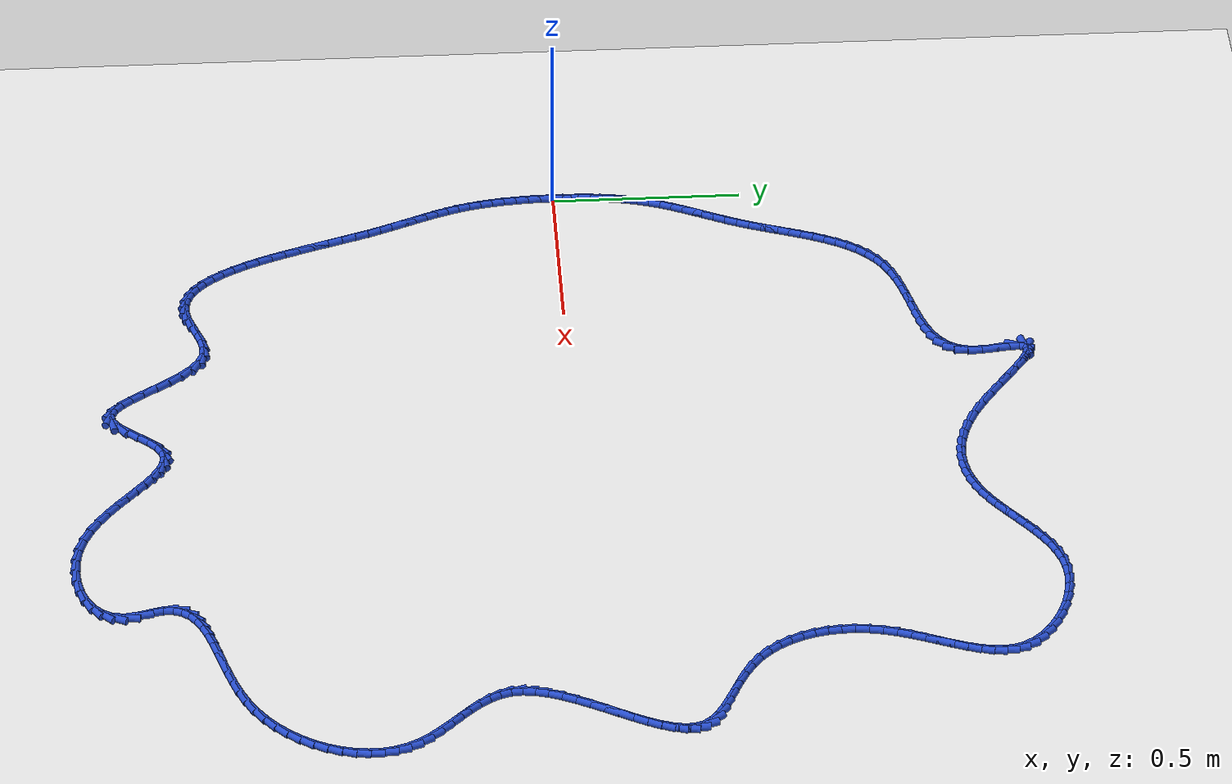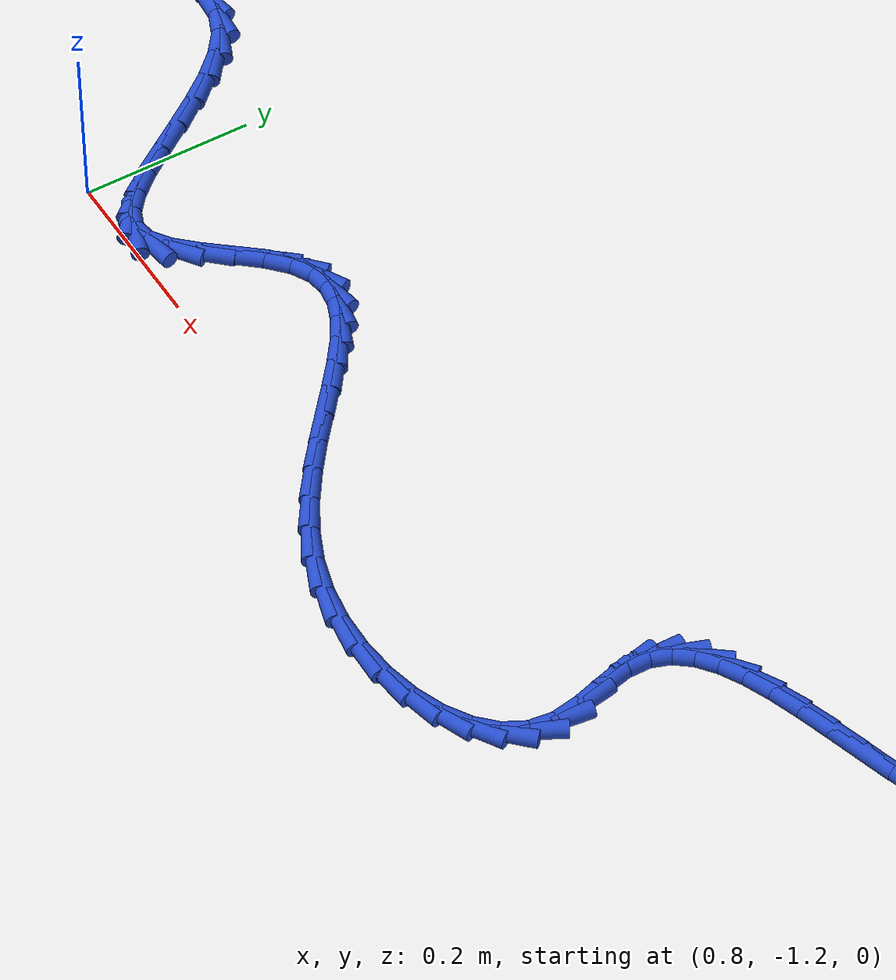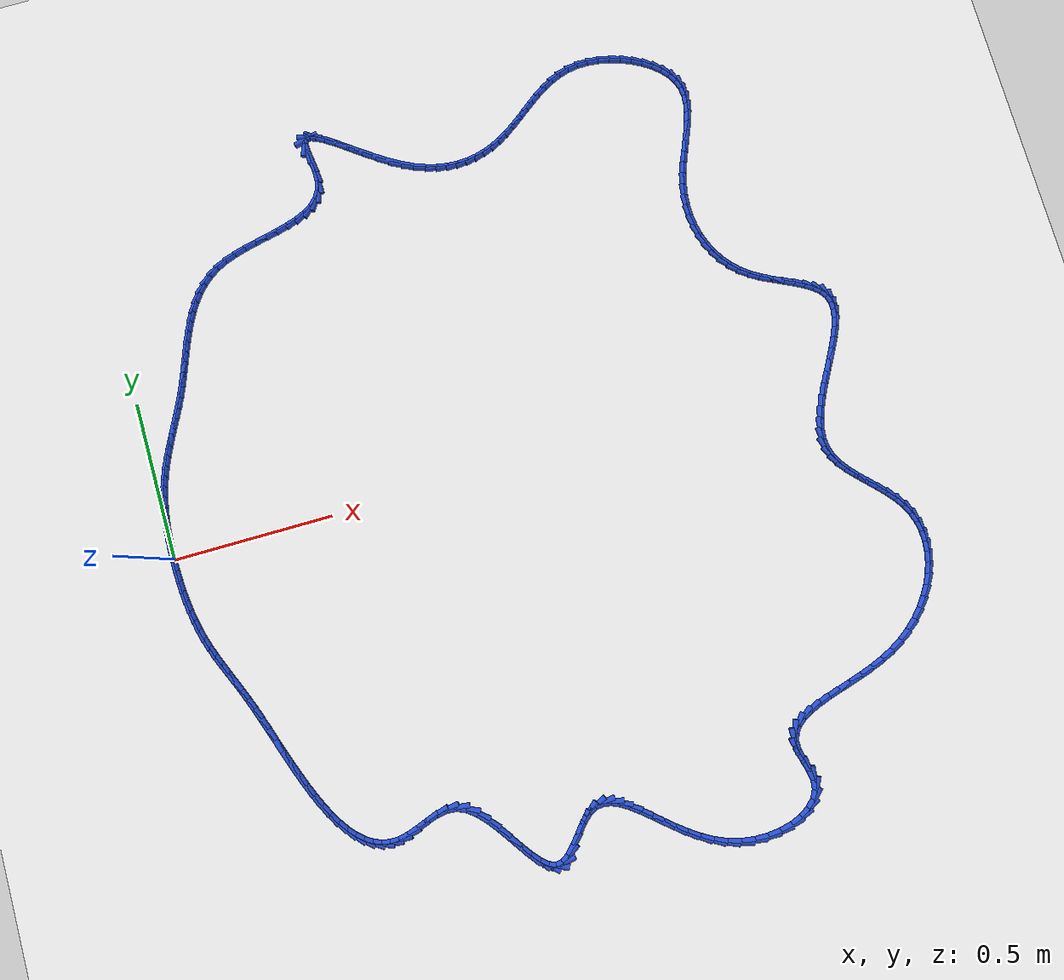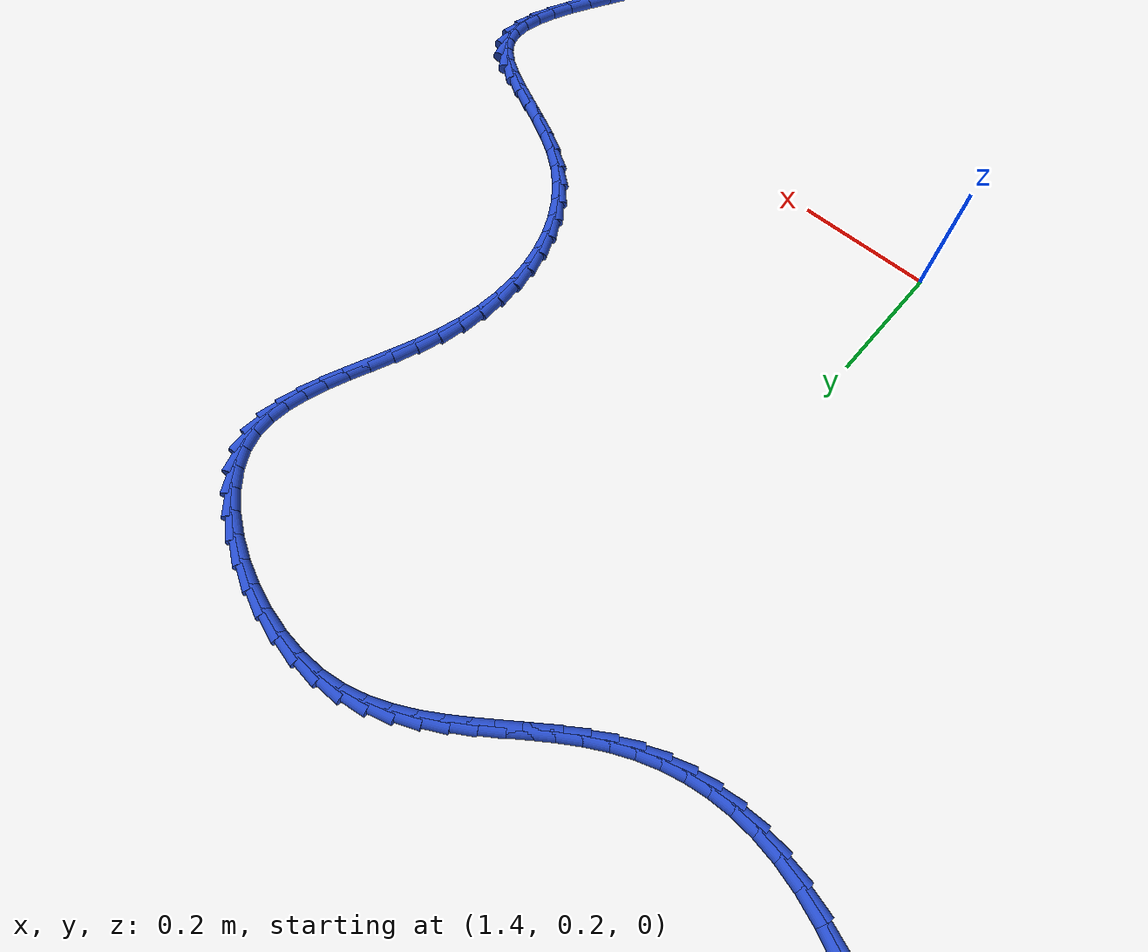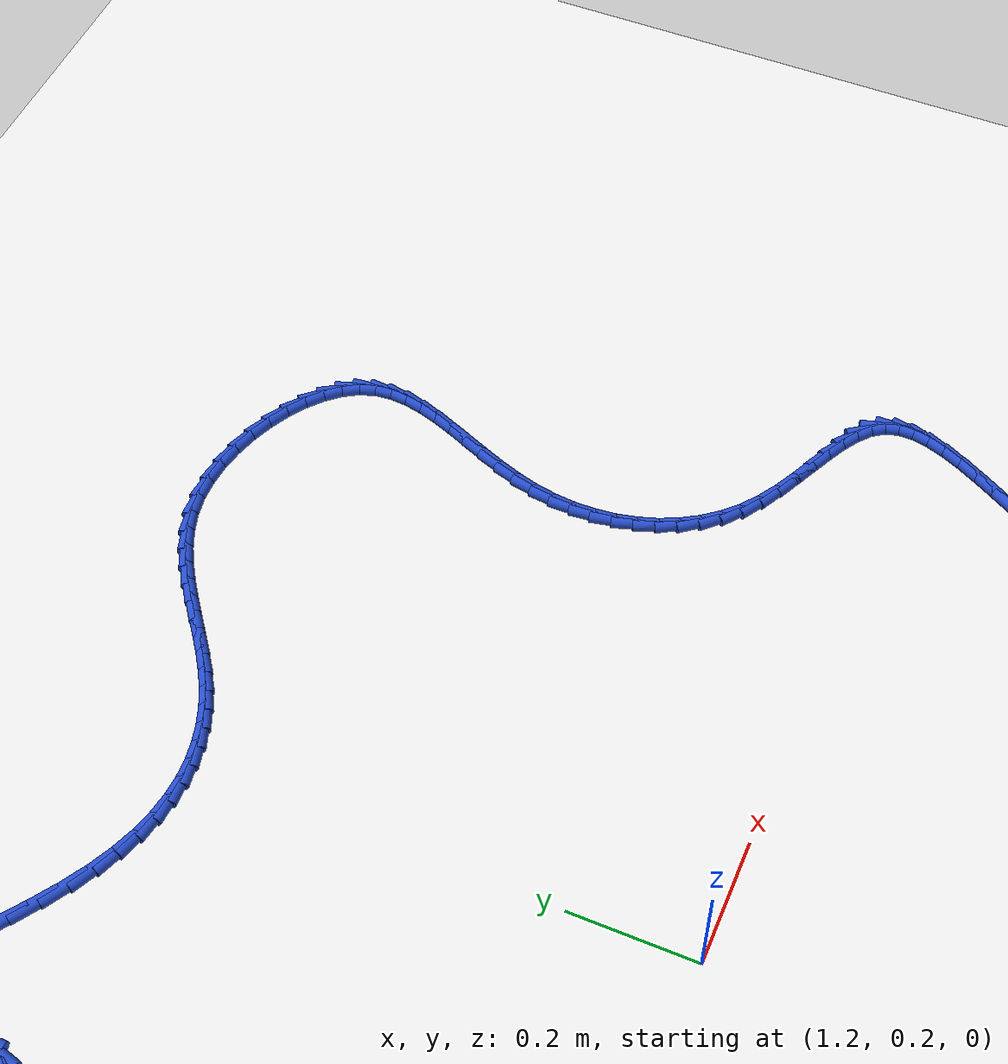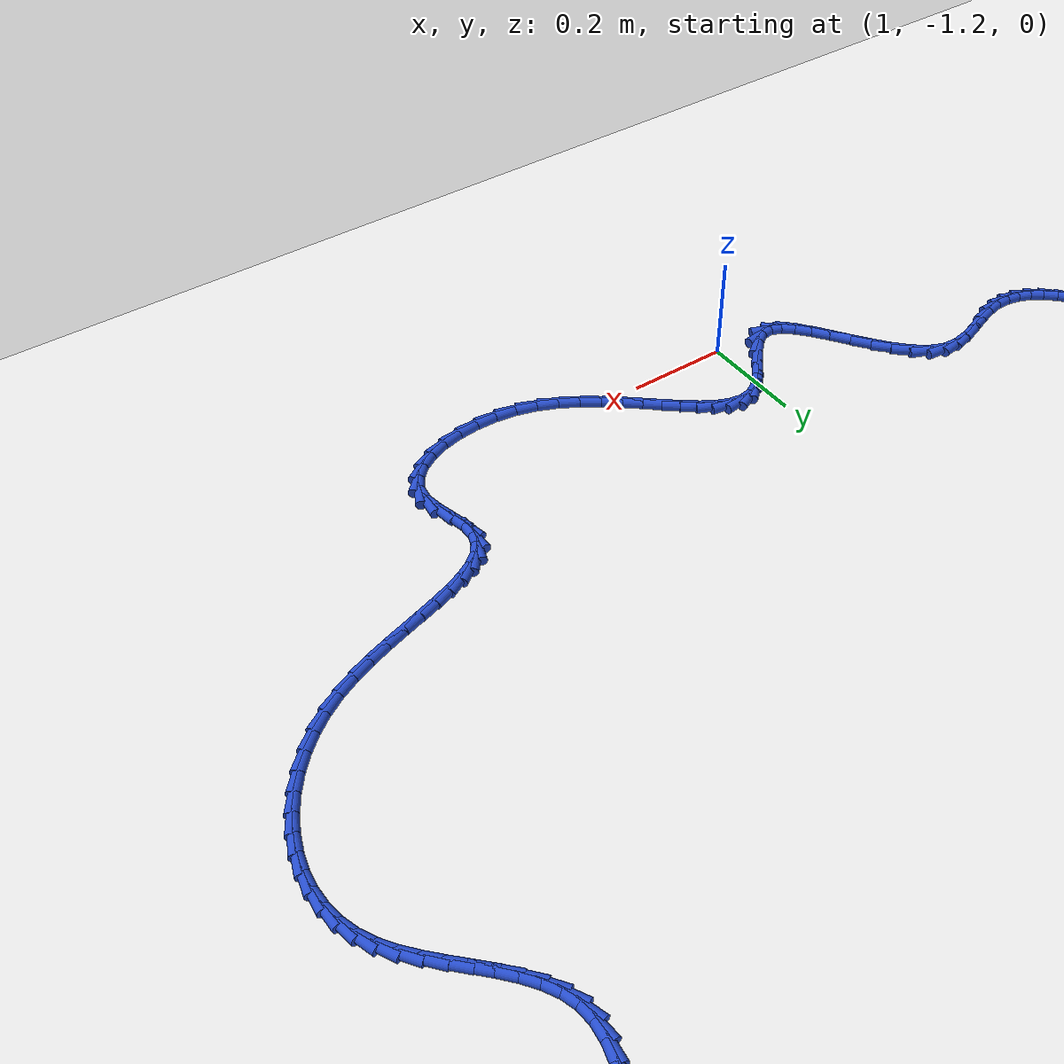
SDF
<sdf version="1.6">
 <world name="default">
  <light name="sun" type="directional">
   <pose>0 0 10 0 -0 0</pose>
   <diffuse>0.8 0.8 0.8 1</diffuse>
   <specular>0.2 0.2 0.2 1</specular>
   <attenuation>
    <range>1000</range>
    <constant>0.9</constant>
    <linear>0.01</linear>
    <quadratic>0.001</quadratic>
   </attenuation>
   <direction>-0.5 0.1 -0.9</direction>
  </light>
  <model name="ground_plane">
   <static>1</static>
   <link name="link">
    <collision name="collision">
     <geometry><plane><normal>0 0 1</normal><size>100 100</size></plane></geometry>
     <surface><friction><ode><mu>100</mu><mu2>50</mu2></ode></friction></surface>
    </collision>
    <visual name="visual">
     <cast_shadows>0</cast_shadows>
     <geometry><plane><normal>0 0 1</normal><size>100 100</size></plane></geometry>
     <material>
      <script><uri>file://media/materials/scripts/gazebo.material</uri><name>Gazebo/WhiteGlow</name></script>
     </material>
    </visual>
   </link>
  </model>
  <gravity>0 0 -9.8</gravity>
  <magnetic_field>6e-06 2.3e-05 -4.2e-05</magnetic_field>
  <atmosphere type="adiabatic"/>
  <physics name="default_physics" default="0" type="ode">
   <max_step_size>0.001</max_step_size>
   <real_time_factor>1</real_time_factor>
   <real_time_update_rate>1000</real_time_update_rate>
  </physics>
  <scene><ambient>0.4 0.4 0.4 1</ambient><background>0.7 0.7 0.7 1</background><shadows>1</shadows></scene>
  <spherical_coordinates>
   <surface_model>EARTH_WGS84</surface_model>
   <latitude_deg>0</latitude_deg>
   <longitude_deg>0</longitude_deg>
   <elevation>0</elevation>
   <heading_deg>0</heading_deg>
  </spherical_coordinates>
  <model name="line">
   <link name="link_0">
    <pose>8.673617379884035e-19 5.551115123125783e-17 0.01 0 1.57 1.5648938598756141</pose>
    <collision name="collision">
     <geometry><cylinder><radius>0.01</radius><length>0.08</length></cylinder></geometry>
    </collision>
    <visual name="visual">
     <material>
      <script><name>Gazebo/Blue</name><uri>file://media/materials/scripts/gazebo.material</uri></script>
     </material>
     <geometry><cylinder><radius>0.01</radius><length>0.08</length></cylinder></geometry>
    </visual>
   </link>
   <link name="link_1">
    <pose>0.00019472981077579024 0.03299087517620522 0.01 0 1.57 1.537072120736988</pose>
    <collision name="collision">
     <geometry><cylinder><radius>0.01</radius><length>0.08</length></cylinder></geometry>
    </collision>
    <visual name="visual">
     <material>
      <script><name>Gazebo/Blue</name><uri>file://media/materials/scripts/gazebo.material</uri></script>
     </material>
     <geometry><cylinder><radius>0.01</radius><length>0.08</length></cylinder></geometry>
    </visual>
   </link>
   <link name="link_2">
    <pose>0.0013032265724894246 0.0658478826522461 0.01 0 1.57 1.5053583056765305</pose>
    <collision name="collision">
     <geometry><cylinder><radius>0.01</radius><length>0.08</length></cylinder></geometry>
    </collision>
    <visual name="visual">
     <material>
      <script><name>Gazebo/Blue</name><uri>file://media/materials/scripts/gazebo.material</uri></script>
     </material>
     <geometry><cylinder><radius>0.01</radius><length>0.08</length></cylinder></geometry>
    </visual>
   </link>
   <link name="link_3">
    <pose>0.0034424732072917373 0.09849239439355043 0.01 0 1.57 1.4695475857500278</pose>
    <collision name="collision">
     <geometry><cylinder><radius>0.01</radius><length>0.08</length></cylinder></geometry>
    </collision>
    <visual name="visual">
     <material>
      <script><name>Gazebo/Blue</name><uri>file://media/materials/scripts/gazebo.material</uri></script>
     </material>
     <geometry><cylinder><radius>0.01</radius><length>0.08</length></cylinder></geometry>
    </visual>
   </link>
   <link name="link_4">
    <pose>0.006729452637333571 0.1308457823655461 0.01 0 1.57 1.4294323296441678</pose>
    <collision name="collision">
     <geometry><cylinder><radius>0.01</radius><length>0.08</length></cylinder></geometry>
    </collision>
    <visual name="visual">
     <material>
      <script><name>Gazebo/Blue</name><uri>file://media/materials/scripts/gazebo.material</uri></script>
     </material>
     <geometry><cylinder><radius>0.01</radius><length>0.08</length></cylinder></geometry>
    </visual>
   </link>
   <link name="link_5">
    <pose>0.011281147784765758 0.16282941853366076 0.01 0 1.57 1.3848194449020697</pose>
    <collision name="collision">
     <geometry><cylinder><radius>0.01</radius><length>0.08</length></cylinder></geometry>
    </collision>
    <visual name="visual">
     <material>
      <script><name>Gazebo/Blue</name><uri>file://media/materials/scripts/gazebo.material</uri></script>
     </material>
     <geometry><cylinder><radius>0.01</radius><length>0.08</length></cylinder></geometry>
    </visual>
   </link>
   <link name="link_6">
    <pose>0.017214541571739128 0.19436467486332223 0.01 0 1.57 1.335553380008307</pose>
    <collision name="collision">
     <geometry><cylinder><radius>0.01</radius><length>0.08</length></cylinder></geometry>
    </collision>
    <visual name="visual">
     <material>
      <script><name>Gazebo/Blue</name><uri>file://media/materials/scripts/gazebo.material</uri></script>
     </material>
     <geometry><cylinder><radius>0.01</radius><length>0.08</length></cylinder></geometry>
    </visual>
   </link>
   <link name="link_7">
    <pose>0.02464661692040453 0.22537292331995823 0.01 0 1.57 1.2815774857083828</pose>
    <collision name="collision">
     <geometry><cylinder><radius>0.01</radius><length>0.08</length></cylinder></geometry>
    </collision>
    <visual name="visual">
     <material>
      <script><name>Gazebo/Blue</name><uri>file://media/materials/scripts/gazebo.material</uri></script>
     </material>
     <geometry><cylinder><radius>0.01</radius><length>0.08</length></cylinder></geometry>
    </visual>
   </link>
   <link name="link_8">
    <pose>0.033693448123322624 0.25577607693114085 0.01 0 1.57 1.2275389181564769</pose>
    <collision name="collision">
     <geometry><cylinder><radius>0.01</radius><length>0.08</length></cylinder></geometry>
    </collision>
    <visual name="visual">
     <material>
      <script><name>Gazebo/Blue</name><uri>file://media/materials/scripts/gazebo.material</uri></script>
     </material>
     <geometry><cylinder><radius>0.01</radius><length>0.08</length></cylinder></geometry>
    </visual>
   </link>
   <link name="link_9">
    <pose>0.04434284580994602 0.28557242595598603 0.01 0 1.57 1.1831659747152563</pose>
    <collision name="collision">
     <geometry><cylinder><radius>0.01</radius><length>0.08</length></cylinder></geometry>
    </collision>
    <visual name="visual">
     <material>
      <script><name>Gazebo/Blue</name><uri>file://media/materials/scripts/gazebo.material</uri></script>
     </material>
     <geometry><cylinder><radius>0.01</radius><length>0.08</length></cylinder></geometry>
    </visual>
   </link>
   <link name="link_10">
    <pose>0.056322996485865265 0.3149148591684351 0.01 0 1.57 1.1499271536958737</pose>
    <collision name="collision">
     <geometry><cylinder><radius>0.01</radius><length>0.08</length></cylinder></geometry>
    </collision>
    <visual name="visual">
     <material>
      <script><name>Gazebo/Blue</name><uri>file://media/materials/scripts/gazebo.material</uri></script>
     </material>
     <geometry><cylinder><radius>0.01</radius><length>0.08</length></cylinder></geometry>
    </visual>
   </link>
   <link name="link_11">
    <pose>0.06933073533798181 0.3439749341288082 0.01 0 1.57 1.1278763799082063</pose>
    <collision name="collision">
     <geometry><cylinder><radius>0.01</radius><length>0.08</length></cylinder></geometry>
    </collision>
    <visual name="visual">
     <material>
      <script><name>Gazebo/Blue</name><uri>file://media/materials/scripts/gazebo.material</uri></script>
     </material>
     <geometry><cylinder><radius>0.01</radius><length>0.08</length></cylinder></geometry>
    </visual>
   </link>
   <link name="link_12">
    <pose>0.0830628975531971 0.3729242083974256 0.01 0 1.57 1.1168914560942909</pose>
    <collision name="collision">
     <geometry><cylinder><radius>0.01</radius><length>0.08</length></cylinder></geometry>
    </collision>
    <visual name="visual">
     <material>
      <script><name>Gazebo/Blue</name><uri>file://media/materials/scripts/gazebo.material</uri></script>
     </material>
     <geometry><cylinder><radius>0.01</radius><length>0.08</length></cylinder></geometry>
    </visual>
   </link>
   <link name="link_13">
    <pose>0.09721631831841256 0.40193423953460766 0.01 0 1.57 1.116760200707132</pose>
    <collision name="collision">
     <geometry><cylinder><radius>0.01</radius><length>0.08</length></cylinder></geometry>
    </collision>
    <visual name="visual">
     <material>
      <script><name>Gazebo/Blue</name><uri>file://media/materials/scripts/gazebo.material</uri></script>
     </material>
     <geometry><cylinder><radius>0.01</radius><length>0.08</length></cylinder></geometry>
    </visual>
   </link>
   <link name="link_14">
    <pose>0.11148783282052956 0.43117658510067436 0.01 0 1.57 1.127224423411209</pose>
    <collision name="collision">
     <geometry><cylinder><radius>0.01</radius><length>0.08</length></cylinder></geometry>
    </collision>
    <visual name="visual">
     <material>
      <script><name>Gazebo/Blue</name><uri>file://media/materials/scripts/gazebo.material</uri></script>
     </material>
     <geometry><cylinder><radius>0.01</radius><length>0.08</length></cylinder></geometry>
    </visual>
   </link>
   <link name="link_15">
    <pose>0.12557427624644954 0.4608228026559458 0.01 0 1.57 1.147984602782549</pose>
    <collision name="collision">
     <geometry><cylinder><radius>0.01</radius><length>0.08</length></cylinder></geometry>
    </collision>
    <visual name="visual">
     <material>
      <script><name>Gazebo/Blue</name><uri>file://media/materials/scripts/gazebo.material</uri></script>
     </material>
     <geometry><cylinder><radius>0.01</radius><length>0.08</length></cylinder></geometry>
    </visual>
   </link>
   <link name="link_16">
    <pose>0.139172483783074 0.49104444976074235 0.01 0 1.57 1.1782766597016914</pose>
    <collision name="collision">
     <geometry><cylinder><radius>0.01</radius><length>0.08</length></cylinder></geometry>
    </collision>
    <visual name="visual">
     <material>
      <script><name>Gazebo/Blue</name><uri>file://media/materials/scripts/gazebo.material</uri></script>
     </material>
     <geometry><cylinder><radius>0.01</radius><length>0.08</length></cylinder></geometry>
    </visual>
   </link>
   <link name="link_17">
    <pose>0.1519902638797746 0.5220050184277414 0.01 0 1.57 1.2069862735411137</pose>
    <collision name="collision">
     <geometry><cylinder><radius>0.01</radius><length>0.08</length></cylinder></geometry>
    </collision>
    <visual name="visual">
     <material>
      <script><name>Gazebo/Blue</name><uri>file://media/materials/scripts/gazebo.material</uri></script>
     </material>
     <geometry><cylinder><radius>0.01</radius><length>0.08</length></cylinder></geometry>
    </visual>
   </link>
   <link name="link_18">
    <pose>0.1640377658721132 0.5536457746152816 0.01 0 1.57 1.222641215555894</pose>
    <collision name="collision">
     <geometry><cylinder><radius>0.01</radius><length>0.08</length></cylinder></geometry>
    </collision>
    <visual name="visual">
     <material>
      <script><name>Gazebo/Blue</name><uri>file://media/materials/scripts/gazebo.material</uri></script>
     </material>
     <geometry><cylinder><radius>0.01</radius><length>0.08</length></cylinder></geometry>
    </visual>
   </link>
   <link name="link_19">
    <pose>0.1756581497875882 0.5856632153619109 0.01 0 1.57 1.2250901159304362</pose>
    <collision name="collision">
     <geometry><cylinder><radius>0.01</radius><length>0.08</length></cylinder></geometry>
    </collision>
    <visual name="visual">
     <material>
      <script><name>Gazebo/Blue</name><uri>file://media/materials/scripts/gazebo.material</uri></script>
     </material>
     <geometry><cylinder><radius>0.01</radius><length>0.08</length></cylinder></geometry>
    </visual>
   </link>
   <link name="link_20">
    <pose>0.1872117008335328 0.6177412503872985 0.01 0 1.57 1.214409447849647</pose>
    <collision name="collision">
     <geometry><cylinder><radius>0.01</radius><length>0.08</length></cylinder></geometry>
    </collision>
    <visual name="visual">
     <material>
      <script><name>Gazebo/Blue</name><uri>file://media/materials/scripts/gazebo.material</uri></script>
     </material>
     <geometry><cylinder><radius>0.01</radius><length>0.08</length></cylinder></geometry>
    </visual>
   </link>
   <link name="link_21">
    <pose>0.1990587042172802 0.6495637894111141 0.01 0 1.57 1.1902800236213078</pose>
    <collision name="collision">
     <geometry><cylinder><radius>0.01</radius><length>0.08</length></cylinder></geometry>
    </collision>
    <visual name="visual">
     <material>
      <script><name>Gazebo/Blue</name><uri>file://media/materials/scripts/gazebo.material</uri></script>
     </material>
     <geometry><cylinder><radius>0.01</radius><length>0.08</length></cylinder></geometry>
    </visual>
   </link>
   <link name="link_22">
    <pose>0.21155944514616312 0.6808147421530261 0.01 0 1.57 1.152022798556756</pose>
    <collision name="collision">
     <geometry><cylinder><radius>0.01</radius><length>0.08</length></cylinder></geometry>
    </collision>
    <visual name="visual">
     <material>
      <script><name>Gazebo/Blue</name><uri>file://media/materials/scripts/gazebo.material</uri></script>
     </material>
     <geometry><cylinder><radius>0.01</radius><length>0.08</length></cylinder></geometry>
    </visual>
   </link>
   <link name="link_23">
    <pose>0.22507420882751505 0.7111780183327046 0.01 0 1.57 1.0986985694848181</pose>
    <collision name="collision">
     <geometry><cylinder><radius>0.01</radius><length>0.08</length></cylinder></geometry>
    </collision>
    <visual name="visual">
     <material>
      <script><name>Gazebo/Blue</name><uri>file://media/materials/scripts/gazebo.material</uri></script>
     </material>
     <geometry><cylinder><radius>0.01</radius><length>0.08</length></cylinder></geometry>
    </visual>
   </link>
   <link name="link_24">
    <pose>0.2399632804686689 0.7403375276698183 0.01 0 1.57 1.0293167525447422</pose>
    <collision name="collision">
     <geometry><cylinder><radius>0.01</radius><length>0.08</length></cylinder></geometry>
    </collision>
    <visual name="visual">
     <material>
      <script><name>Gazebo/Blue</name><uri>file://media/materials/scripts/gazebo.material</uri></script>
     </material>
     <geometry><cylinder><radius>0.01</radius><length>0.08</length></cylinder></geometry>
    </visual>
   </link>
   <link name="link_25">
    <pose>0.25658694527695786 0.767977179884037 0.01 0 1.57 0.9432123937851087</pose>
    <collision name="collision">
     <geometry><cylinder><radius>0.01</radius><length>0.08</length></cylinder></geometry>
    </collision>
    <visual name="visual">
     <material>
      <script><name>Gazebo/Blue</name><uri>file://media/materials/scripts/gazebo.material</uri></script>
     </material>
     <geometry><cylinder><radius>0.01</radius><length>0.08</length></cylinder></geometry>
    </visual>
   </link>
   <link name="link_26">
    <pose>0.27530548845971486 0.7937808846950298 0.01 0 1.57 0.8406222613339868</pose>
    <collision name="collision">
     <geometry><cylinder><radius>0.01</radius><length>0.08</length></cylinder></geometry>
    </collision>
    <visual name="visual">
     <material>
      <script><name>Gazebo/Blue</name><uri>file://media/materials/scripts/gazebo.material</uri></script>
     </material>
     <geometry><cylinder><radius>0.01</radius><length>0.08</length></cylinder></geometry>
    </visual>
   </link>
   <link name="link_27">
    <pose>0.2964791952242731 0.8174325518224657 0.01 0 1.57 0.7233691613524007</pose>
    <collision name="collision">
     <geometry><cylinder><radius>0.01</radius><length>0.08</length></cylinder></geometry>
    </collision>
    <visual name="visual">
     <material>
      <script><name>Gazebo/Blue</name><uri>file://media/materials/scripts/gazebo.material</uri></script>
     </material>
     <geometry><cylinder><radius>0.01</radius><length>0.08</length></cylinder></geometry>
    </visual>
   </link>
   <link name="link_28">
    <pose>0.32046835077796565 0.8386160909860143 0.01 0 1.57 0.595341717369687</pose>
    <collision name="collision">
     <geometry><cylinder><radius>0.01</radius><length>0.08</length></cylinder></geometry>
    </collision>
    <visual name="visual">
     <material>
      <script><name>Gazebo/Blue</name><uri>file://media/materials/scripts/gazebo.material</uri></script>
     </material>
     <geometry><cylinder><radius>0.01</radius><length>0.08</length></cylinder></geometry>
    </visual>
   </link>
   <link name="link_29">
    <pose>0.3476332403281257 0.8570154119053449 0.01 0 1.57 0.4645721290135875</pose>
    <collision name="collision">
     <geometry><cylinder><radius>0.01</radius><length>0.08</length></cylinder></geometry>
    </collision>
    <visual name="visual">
     <material>
      <script><name>Gazebo/Blue</name><uri>file://media/materials/scripts/gazebo.material</uri></script>
     </material>
     <geometry><cylinder><radius>0.01</radius><length>0.08</length></cylinder></geometry>
    </visual>
   </link>
   <link name="link_30">
    <pose>0.37826789799194477 0.8723681600629022 0.01 0 1.57 0.3590655584564902</pose>
    <collision name="collision">
     <geometry><cylinder><radius>0.01</radius><length>0.08</length></cylinder></geometry>
    </collision>
    <visual name="visual">
     <material>
      <script><name>Gazebo/Blue</name><uri>file://media/materials/scripts/gazebo.material</uri></script>
     </material>
     <geometry><cylinder><radius>0.01</radius><length>0.08</length></cylinder></geometry>
    </visual>
   </link>
   <link name="link_31">
    <pose>0.4119354476577591 0.8850048167508436 0.01 0 1.57 0.28827498622024916</pose>
    <collision name="collision">
     <geometry><cylinder><radius>0.01</radius><length>0.08</length></cylinder></geometry>
    </collision>
    <visual name="visual">
     <material>
      <script><name>Gazebo/Blue</name><uri>file://media/materials/scripts/gazebo.material</uri></script>
     </material>
     <geometry><cylinder><radius>0.01</radius><length>0.08</length></cylinder></geometry>
    </visual>
   </link>
   <link name="link_32">
    <pose>0.4477454542661981 0.8956237415251675 0.01 0 1.57 0.2460261230389155</pose>
    <collision name="collision">
     <geometry><cylinder><radius>0.01</radius><length>0.08</length></cylinder></geometry>
    </collision>
    <visual name="visual">
     <material>
      <script><name>Gazebo/Blue</name><uri>file://media/materials/scripts/gazebo.material</uri></script>
     </material>
     <geometry><cylinder><radius>0.01</radius><length>0.08</length></cylinder></geometry>
    </visual>
   </link>
   <link name="link_33">
    <pose>0.4848006923347947 0.9049288016031641 0.01 0 1.57 0.22841125643875623</pose>
    <collision name="collision">
     <geometry><cylinder><radius>0.01</radius><length>0.08</length></cylinder></geometry>
    </collision>
    <visual name="visual">
     <material>
      <script><name>Gazebo/Blue</name><uri>file://media/materials/scripts/gazebo.material</uri></script>
     </material>
     <geometry><cylinder><radius>0.01</radius><length>0.08</length></cylinder></geometry>
    </visual>
   </link>
   <link name="link_34">
    <pose>0.5222039363810819 0.913623864202123 0.01 0 1.57 0.23410687317102608</pose>
    <collision name="collision">
     <geometry><cylinder><radius>0.01</radius><length>0.08</length></cylinder></geometry>
    </collision>
    <visual name="visual">
     <material>
      <script><name>Gazebo/Blue</name><uri>file://media/materials/scripts/gazebo.material</uri></script>
     </material>
     <geometry><cylinder><radius>0.01</radius><length>0.08</length></cylinder></geometry>
    </visual>
   </link>
   <link name="link_35">
    <pose>0.5590579609225923 0.9224127965393341 0.01 0 1.57 0.26441250881149453</pose>
    <collision name="collision">
     <geometry><cylinder><radius>0.01</radius><length>0.08</length></cylinder></geometry>
    </collision>
    <visual name="visual">
     <material>
      <script><name>Gazebo/Blue</name><uri>file://media/materials/scripts/gazebo.material</uri></script>
     </material>
     <geometry><cylinder><radius>0.01</radius><length>0.08</length></cylinder></geometry>
    </visual>
   </link>
   <link name="link_36">
    <pose>0.5944655404768591 0.9319994658320871 0.01 0 1.57 0.3235723814605655</pose>
    <collision name="collision">
     <geometry><cylinder><radius>0.01</radius><length>0.08</length></cylinder></geometry>
    </collision>
    <visual name="visual">
     <material>
      <script><name>Gazebo/Blue</name><uri>file://media/materials/scripts/gazebo.material</uri></script>
     </material>
     <geometry><cylinder><radius>0.01</radius><length>0.08</length></cylinder></geometry>
    </visual>
   </link>
   <link name="link_37">
    <pose>0.6275294495614145 0.9430877392976718 0.01 0 1.57 0.41931783271356454</pose>
    <collision name="collision">
     <geometry><cylinder><radius>0.01</radius><length>0.08</length></cylinder></geometry>
    </collision>
    <visual name="visual">
     <material>
      <script><name>Gazebo/Blue</name><uri>file://media/materials/scripts/gazebo.material</uri></script>
     </material>
     <geometry><cylinder><radius>0.01</radius><length>0.08</length></cylinder></geometry>
    </visual>
   </link>
   <link name="link_38">
    <pose>0.6573524626937927 0.9563814841533786 0.01 0 1.57 0.562788582438893</pose>
    <collision name="collision">
     <geometry><cylinder><radius>0.01</radius><length>0.08</length></cylinder></geometry>
    </collision>
    <visual name="visual">
     <material>
      <script><name>Gazebo/Blue</name><uri>file://media/materials/scripts/gazebo.material</uri></script>
     </material>
     <geometry><cylinder><radius>0.01</radius><length>0.08</length></cylinder></geometry>
    </visual>
   </link>
   <link name="link_39">
    <pose>0.6830373543915254 0.9725845676164968 0.01 0 1.57 0.7648094922013549</pose>
    <collision name="collision">
     <geometry><cylinder><radius>0.01</radius><length>0.08</length></cylinder></geometry>
    </collision>
    <visual name="visual">
     <material>
      <script><name>Gazebo/Blue</name><uri>file://media/materials/scripts/gazebo.material</uri></script>
     </material>
     <geometry><cylinder><radius>0.01</radius><length>0.08</length></cylinder></geometry>
    </visual>
   </link>
   <link name="link_40">
    <pose>0.7036868991721461 0.9924008569043166 0.01 0 1.57 1.0231885554680273</pose>
    <collision name="collision">
     <geometry><cylinder><radius>0.01</radius><length>0.08</length></cylinder></geometry>
    </collision>
    <visual name="visual">
     <material>
      <script><name>Gazebo/Blue</name><uri>file://media/materials/scripts/gazebo.material</uri></script>
     </material>
     <geometry><cylinder><radius>0.01</radius><length>0.08</length></cylinder></geometry>
    </visual>
   </link>
   <link name="link_41">
    <pose>0.7184038715531872 1.0165342192341273 0.01 0 1.57 1.3065886197410457</pose>
    <collision name="collision">
     <geometry><cylinder><radius>0.01</radius><length>0.08</length></cylinder></geometry>
    </collision>
    <visual name="visual">
     <material>
      <script><name>Gazebo/Blue</name><uri>file://media/materials/scripts/gazebo.material</uri></script>
     </material>
     <geometry><cylinder><radius>0.01</radius><length>0.08</length></cylinder></geometry>
    </visual>
   </link>
   <link name="link_42">
    <pose>0.7262910460521822 1.0456885218232195 0.01 0 1.57 1.5539494372116864</pose>
    <collision name="collision">
     <geometry><cylinder><radius>0.01</radius><length>0.08</length></cylinder></geometry>
    </collision>
    <visual name="visual">
     <material>
      <script><name>Gazebo/Blue</name><uri>file://media/materials/scripts/gazebo.material</uri></script>
     </material>
     <geometry><cylinder><radius>0.01</radius><length>0.08</length></cylinder></geometry>
    </visual>
   </link>
   <link name="link_43">
    <pose>0.7268709877321838 1.0801095234091158 0.01 0 1.57 -1.4595977136403115</pose>
    <collision name="collision">
     <geometry><cylinder><radius>0.01</radius><length>0.08</length></cylinder></geometry>
    </collision>
    <visual name="visual">
     <material>
      <script><name>Gazebo/Blue</name><uri>file://media/materials/scripts/gazebo.material</uri></script>
     </material>
     <geometry><cylinder><radius>0.01</radius><length>0.08</length></cylinder></geometry>
    </visual>
   </link>
   <link name="link_44">
    <pose>0.7227930524213972 1.1166307825755817 0.01 0 1.57 -1.4338027023843385</pose>
    <collision name="collision">
     <geometry><cylinder><radius>0.01</radius><length>0.08</length></cylinder></geometry>
    </collision>
    <visual name="visual">
     <material>
      <script><name>Gazebo/Blue</name><uri>file://media/materials/scripts/gazebo.material</uri></script>
     </material>
     <geometry><cylinder><radius>0.01</radius><length>0.08</length></cylinder></geometry>
    </visual>
   </link>
   <link name="link_45">
    <pose>0.7181175888915501 1.1505460713646976 0.01 0 1.57 -1.5254897802373781</pose>
    <collision name="collision">
     <geometry><cylinder><radius>0.01</radius><length>0.08</length></cylinder></geometry>
    </collision>
    <visual name="visual">
     <material>
      <script><name>Gazebo/Blue</name><uri>file://media/materials/scripts/gazebo.material</uri></script>
     </material>
     <geometry><cylinder><radius>0.01</radius><length>0.08</length></cylinder></geometry>
    </visual>
   </link>
   <link name="link_46">
    <pose>0.7169118089152868 1.1771416723718424 0.01 0 1.57 1.1968703611762284</pose>
    <collision name="collision">
     <geometry><cylinder><radius>0.01</radius><length>0.08</length></cylinder></geometry>
    </collision>
    <visual name="visual">
     <material>
      <script><name>Gazebo/Blue</name><uri>file://media/materials/scripts/gazebo.material</uri></script>
     </material>
     <geometry><cylinder><radius>0.01</radius><length>0.08</length></cylinder></geometry>
    </visual>
   </link>
   <link name="link_47">
    <pose>0.7228337122523797 1.1922336825140523 0.01 0 1.57 0.25409814333508574</pose>
    <collision name="collision">
     <geometry><cylinder><radius>0.01</radius><length>0.08</length></cylinder></geometry>
    </collision>
    <visual name="visual">
     <material>
      <script><name>Gazebo/Blue</name><uri>file://media/materials/scripts/gazebo.material</uri></script>
     </material>
     <geometry><cylinder><radius>0.01</radius><length>0.08</length></cylinder></geometry>
    </visual>
   </link>
   <link name="link_48">
    <pose>0.7363667322216277 1.1957483682844585 0.01 0 1.57 -0.2992763449349352</pose>
    <collision name="collision">
     <geometry><cylinder><radius>0.01</radius><length>0.08</length></cylinder></geometry>
    </collision>
    <visual name="visual">
     <material>
      <script><name>Gazebo/Blue</name><uri>file://media/materials/scripts/gazebo.material</uri></script>
     </material>
     <geometry><cylinder><radius>0.01</radius><length>0.08</length></cylinder></geometry>
    </visual>
   </link>
   <link name="link_49">
    <pose>0.756510462443299 1.1895331507332327 0.01 0 1.57 -0.50065525260731</pose>
    <collision name="collision">
     <geometry><cylinder><radius>0.01</radius><length>0.08</length></cylinder></geometry>
    </collision>
    <visual name="visual">
     <material>
      <script><name>Gazebo/Blue</name><uri>file://media/materials/scripts/gazebo.material</uri></script>
     </material>
     <geometry><cylinder><radius>0.01</radius><length>0.08</length></cylinder></geometry>
    </visual>
   </link>
   <link name="link_50">
    <pose>0.7822560862648624 1.1754463398454695 0.01 0 1.57 -0.5851285870695462</pose>
    <collision name="collision">
     <geometry><cylinder><radius>0.01</radius><length>0.08</length></cylinder></geometry>
    </collision>
    <visual name="visual">
     <material>
      <script><name>Gazebo/Blue</name><uri>file://media/materials/scripts/gazebo.material</uri></script>
     </material>
     <geometry><cylinder><radius>0.01</radius><length>0.08</length></cylinder></geometry>
    </visual>
   </link>
   <link name="link_51">
    <pose>0.8125947870337872 1.1553462456062638 0.01 0 1.57 -0.6207252338198733</pose>
    <collision name="collision">
     <geometry><cylinder><radius>0.01</radius><length>0.08</length></cylinder></geometry>
    </collision>
    <visual name="visual">
     <material>
      <script><name>Gazebo/Blue</name><uri>file://media/materials/scripts/gazebo.material</uri></script>
     </material>
     <geometry><cylinder><radius>0.01</radius><length>0.08</length></cylinder></geometry>
    </visual>
   </link>
   <link name="link_52">
    <pose>0.8465177480975422 1.1310911780007105 0.01 0 1.57 -0.628929538897971</pose>
    <collision name="collision">
     <geometry><cylinder><radius>0.01</radius><length>0.08</length></cylinder></geometry>
    </collision>
    <visual name="visual">
     <material>
      <script><name>Gazebo/Blue</name><uri>file://media/materials/scripts/gazebo.material</uri></script>
     </material>
     <geometry><cylinder><radius>0.01</radius><length>0.08</length></cylinder></geometry>
    </visual>
   </link>
   <link name="link_53">
    <pose>0.8830161528035964 1.1045394470139043 0.01 0 1.57 -0.6167752892217245</pose>
    <collision name="collision">
     <geometry><cylinder><radius>0.01</radius><length>0.08</length></cylinder></geometry>
    </collision>
    <visual name="visual">
     <material>
      <script><name>Gazebo/Blue</name><uri>file://media/materials/scripts/gazebo.material</uri></script>
     </material>
     <geometry><cylinder><radius>0.01</radius><length>0.08</length></cylinder></geometry>
    </visual>
   </link>
   <link name="link_54">
    <pose>0.9210811844994192 1.0775493626309396 0.01 0 1.57 -0.5847973897527646</pose>
    <collision name="collision">
     <geometry><cylinder><radius>0.01</radius><length>0.08</length></cylinder></geometry>
    </collision>
    <visual name="visual">
     <material>
      <script><name>Gazebo/Blue</name><uri>file://media/materials/scripts/gazebo.material</uri></script>
     </material>
     <geometry><cylinder><radius>0.01</radius><length>0.08</length></cylinder></geometry>
    </visual>
   </link>
   <link name="link_55">
    <pose>0.9597040265324792 1.051979234836912 0.01 0 1.57 -0.5286579283581512</pose>
    <collision name="collision">
     <geometry><cylinder><radius>0.01</radius><length>0.08</length></cylinder></geometry>
    </collision>
    <visual name="visual">
     <material>
      <script><name>Gazebo/Blue</name><uri>file://media/materials/scripts/gazebo.material</uri></script>
     </material>
     <geometry><cylinder><radius>0.01</radius><length>0.08</length></cylinder></geometry>
    </visual>
   </link>
   <link name="link_56">
    <pose>0.9978793618882638 1.0296804249708775 0.01 0 1.57 -0.448992332908829</pose>
    <collision name="collision">
     <geometry><cylinder><radius>0.01</radius><length>0.08</length></cylinder></geometry>
    </collision>
    <visual name="visual">
     <material>
      <script><name>Gazebo/Blue</name><uri>file://media/materials/scripts/gazebo.material</uri></script>
     </material>
     <geometry><cylinder><radius>0.01</radius><length>0.08</length></cylinder></geometry>
    </visual>
   </link>
   <link name="link_57">
    <pose>1.0349458526325543 1.0118213126288893 0.01 0 1.57 -0.3594556458274122</pose>
    <collision name="collision">
     <geometry><cylinder><radius>0.01</radius><length>0.08</length></cylinder></geometry>
    </collision>
    <visual name="visual">
     <material>
      <script><name>Gazebo/Blue</name><uri>file://media/materials/scripts/gazebo.material</uri></script>
     </material>
     <geometry><cylinder><radius>0.01</radius><length>0.08</length></cylinder></geometry>
    </visual>
   </link>
   <link name="link_58">
    <pose>1.0708712421454343 0.9983212158298612 0.01 0 1.57 -0.26247632756812644</pose>
    <collision name="collision">
     <geometry><cylinder><radius>0.01</radius><length>0.08</length></cylinder></geometry>
    </collision>
    <visual name="visual">
     <material>
      <script><name>Gazebo/Blue</name><uri>file://media/materials/scripts/gazebo.material</uri></script>
     </material>
     <geometry><cylinder><radius>0.01</radius><length>0.08</length></cylinder></geometry>
    </visual>
   </link>
   <link name="link_59">
    <pose>1.1056903930555 0.9889661851239498 0.01 0 1.57 -0.15935639312435537</pose>
    <collision name="collision">
     <geometry><cylinder><radius>0.01</radius><length>0.08</length></cylinder></geometry>
    </collision>
    <visual name="visual">
     <material>
      <script><name>Gazebo/Blue</name><uri>file://media/materials/scripts/gazebo.material</uri></script>
     </material>
     <geometry><cylinder><radius>0.01</radius><length>0.08</length></cylinder></geometry>
    </visual>
   </link>
   <link name="link_60">
    <pose>1.139438167991345 0.9835422710613104 0.01 0 1.57 -0.05212885486206602</pose>
    <collision name="collision">
     <geometry><cylinder><radius>0.01</radius><length>0.08</length></cylinder></geometry>
    </collision>
    <visual name="visual">
     <material>
      <script><name>Gazebo/Blue</name><uri>file://media/materials/scripts/gazebo.material</uri></script>
     </material>
     <geometry><cylinder><radius>0.01</radius><length>0.08</length></cylinder></geometry>
    </visual>
   </link>
   <link name="link_61">
    <pose>1.1721494295815653 0.9818355241920991 0.01 0 1.57 0.056593332426725054</pose>
    <collision name="collision">
     <geometry><cylinder><radius>0.01</radius><length>0.08</length></cylinder></geometry>
    </collision>
    <visual name="visual">
     <material>
      <script><name>Gazebo/Blue</name><uri>file://media/materials/scripts/gazebo.material</uri></script>
     </material>
     <geometry><cylinder><radius>0.01</radius><length>0.08</length></cylinder></geometry>
    </visual>
   </link>
   <link name="link_62">
    <pose>1.2038590404547553 0.9836319950664709 0.01 0 1.57 0.16394373681483182</pose>
    <collision name="collision">
     <geometry><cylinder><radius>0.01</radius><length>0.08</length></cylinder></geometry>
    </collision>
    <visual name="visual">
     <material>
      <script><name>Gazebo/Blue</name><uri>file://media/materials/scripts/gazebo.material</uri></script>
     </material>
     <geometry><cylinder><radius>0.01</radius><length>0.08</length></cylinder></geometry>
    </visual>
   </link>
   <link name="link_63">
    <pose>1.23460186323951 0.988717734234582 0.01 0 1.57 0.26721386278445103</pose>
    <collision name="collision">
     <geometry><cylinder><radius>0.01</radius><length>0.08</length></cylinder></geometry>
    </collision>
    <visual name="visual">
     <material>
      <script><name>Gazebo/Blue</name><uri>file://media/materials/scripts/gazebo.material</uri></script>
     </material>
     <geometry><cylinder><radius>0.01</radius><length>0.08</length></cylinder></geometry>
    </visual>
   </link>
   <link name="link_64">
    <pose>1.264412760564425 0.9968787922465879 0.01 0 1.57 0.36420948067374337</pose>
    <collision name="collision">
     <geometry><cylinder><radius>0.01</radius><length>0.08</length></cylinder></geometry>
    </collision>
    <visual name="visual">
     <material>
      <script><name>Gazebo/Blue</name><uri>file://media/materials/scripts/gazebo.material</uri></script>
     </material>
     <geometry><cylinder><radius>0.01</radius><length>0.08</length></cylinder></geometry>
    </visual>
   </link>
   <link name="link_65">
    <pose>1.2933265950580946 1.0079012196526445 0.01 0 1.57 0.45344432547468283</pose>
    <collision name="collision">
     <geometry><cylinder><radius>0.01</radius><length>0.08</length></cylinder></geometry>
    </collision>
    <visual name="visual">
     <material>
      <script><name>Gazebo/Blue</name><uri>file://media/materials/scripts/gazebo.material</uri></script>
     </material>
     <geometry><cylinder><radius>0.01</radius><length>0.08</length></cylinder></geometry>
    </visual>
   </link>
   <link name="link_66">
    <pose>1.3213782293491136 1.0215710670029072 0.01 0 1.57 0.5337361373017906</pose>
    <collision name="collision">
     <geometry><cylinder><radius>0.01</radius><length>0.08</length></cylinder></geometry>
    </collision>
    <visual name="visual">
     <material>
      <script><name>Gazebo/Blue</name><uri>file://media/materials/scripts/gazebo.material</uri></script>
     </material>
     <geometry><cylinder><radius>0.01</radius><length>0.08</length></cylinder></geometry>
    </visual>
   </link>
   <link name="link_67">
    <pose>1.34860862133253 1.0376627798742941 0.01 0 1.57 0.597008283840292</pose>
    <collision name="collision">
     <geometry><cylinder><radius>0.01</radius><length>0.08</length></cylinder></geometry>
    </collision>
    <visual name="visual">
     <material>
      <script><name>Gazebo/Blue</name><uri>file://media/materials/scripts/gazebo.material</uri></script>
     </material>
     <geometry><cylinder><radius>0.01</radius><length>0.08</length></cylinder></geometry>
    </visual>
   </link>
   <link name="link_68">
    <pose>1.375178117604499 1.0557234958676043 0.01 0 1.57 0.6370212797496714</pose>
    <collision name="collision">
     <geometry><cylinder><radius>0.01</radius><length>0.08</length></cylinder></geometry>
    </collision>
    <visual name="visual">
     <material>
      <script><name>Gazebo/Blue</name><uri>file://media/materials/scripts/gazebo.material</uri></script>
     </material>
     <geometry><cylinder><radius>0.01</radius><length>0.08</length></cylinder></geometry>
    </visual>
   </link>
   <link name="link_69">
    <pose>1.4013559264389752 1.0750930873447317 0.01 0 1.57 0.6548543568633062</pose>
    <collision name="collision">
     <geometry><cylinder><radius>0.01</radius><length>0.08</length></cylinder></geometry>
    </collision>
    <visual name="visual">
     <material>
      <script><name>Gazebo/Blue</name><uri>file://media/materials/scripts/gazebo.material</uri></script>
     </material>
     <geometry><cylinder><radius>0.01</radius><length>0.08</length></cylinder></geometry>
    </visual>
   </link>
   <link name="link_70">
    <pose>1.4274152403465667 1.0951038409516558 0.01 0 1.57 0.651357179426609</pose>
    <collision name="collision">
     <geometry><cylinder><radius>0.01</radius><length>0.08</length></cylinder></geometry>
    </collision>
    <visual name="visual">
     <material>
      <script><name>Gazebo/Blue</name><uri>file://media/materials/scripts/gazebo.material</uri></script>
     </material>
     <geometry><cylinder><radius>0.01</radius><length>0.08</length></cylinder></geometry>
    </visual>
   </link>
   <link name="link_71">
    <pose>1.453629251837882 1.1150880433343573 0.01 0 1.57 0.6266819886396803</pose>
    <collision name="collision">
     <geometry><cylinder><radius>0.01</radius><length>0.08</length></cylinder></geometry>
    </collision>
    <visual name="visual">
     <material>
      <script><name>Gazebo/Blue</name><uri>file://media/materials/scripts/gazebo.material</uri></script>
     </material>
     <geometry><cylinder><radius>0.01</radius><length>0.08</length></cylinder></geometry>
    </visual>
   </link>
   <link name="link_72">
    <pose>1.4802711534235282 1.1343779811388155 0.01 0 1.57 0.5803504668529568</pose>
    <collision name="collision">
     <geometry><cylinder><radius>0.01</radius><length>0.08</length></cylinder></geometry>
    </collision>
    <visual name="visual">
     <material>
      <script><name>Gazebo/Blue</name><uri>file://media/materials/scripts/gazebo.material</uri></script>
     </material>
     <geometry><cylinder><radius>0.01</radius><length>0.08</length></cylinder></geometry>
    </visual>
   </link>
   <link name="link_73">
    <pose>1.5076141376141132 1.15230594101101 0.01 0 1.57 0.5115792150474214</pose>
    <collision name="collision">
     <geometry><cylinder><radius>0.01</radius><length>0.08</length></cylinder></geometry>
    </collision>
    <visual name="visual">
     <material>
      <script><name>Gazebo/Blue</name><uri>file://media/materials/scripts/gazebo.material</uri></script>
     </material>
     <geometry><cylinder><radius>0.01</radius><length>0.08</length></cylinder></geometry>
    </visual>
   </link>
   <link name="link_74">
    <pose>1.5359313969202466 1.1682042095969212 0.01 0 1.57 0.4199455316465645</pose>
    <collision name="collision">
     <geometry><cylinder><radius>0.01</radius><length>0.08</length></cylinder></geometry>
    </collision>
    <visual name="visual">
     <material>
      <script><name>Gazebo/Blue</name><uri>file://media/materials/scripts/gazebo.material</uri></script>
     </material>
     <geometry><cylinder><radius>0.01</radius><length>0.08</length></cylinder></geometry>
    </visual>
   </link>
   <link name="link_75">
    <pose>1.5654961238525353 1.1814050735425288 0.01 0 1.57 0.30644357248725673</pose>
    <collision name="collision">
     <geometry><cylinder><radius>0.01</radius><length>0.08</length></cylinder></geometry>
    </collision>
    <visual name="visual">
     <material>
      <script><name>Gazebo/Blue</name><uri>file://media/materials/scripts/gazebo.material</uri></script>
     </material>
     <geometry><cylinder><radius>0.01</radius><length>0.08</length></cylinder></geometry>
    </visual>
   </link>
   <link name="link_76">
    <pose>1.5965815109215875 1.1912408194938124 0.01 0 1.57 0.17472172366934946</pose>
    <collision name="collision">
     <geometry><cylinder><radius>0.01</radius><length>0.08</length></cylinder></geometry>
    </collision>
    <visual name="visual">
     <material>
      <script><name>Gazebo/Blue</name><uri>file://media/materials/scripts/gazebo.material</uri></script>
     </material>
     <geometry><cylinder><radius>0.01</radius><length>0.08</length></cylinder></geometry>
    </visual>
   </link>
   <link name="link_77">
    <pose>1.6294598441910815 1.197044557317005 0.01 0 1.57 0.03937473053387125</pose>
    <collision name="collision">
     <geometry><cylinder><radius>0.01</radius><length>0.08</length></cylinder></geometry>
    </collision>
    <visual name="visual">
     <material>
      <script><name>Gazebo/Blue</name><uri>file://media/materials/scripts/gazebo.material</uri></script>
     </material>
     <geometry><cylinder><radius>0.01</radius><length>0.08</length></cylinder></geometry>
    </visual>
   </link>
   <link name="link_78">
    <pose>1.6641166099041123 1.1984098637775236 0.01 0 1.57 -0.07958024891510279</pose>
    <collision name="collision">
     <geometry><cylinder><radius>0.01</radius><length>0.08</length></cylinder></geometry>
    </collision>
    <visual name="visual">
     <material>
      <script><name>Gazebo/Blue</name><uri>file://media/materials/scripts/gazebo.material</uri></script>
     </material>
     <geometry><cylinder><radius>0.01</radius><length>0.08</length></cylinder></geometry>
    </visual>
   </link>
   <link name="link_79">
    <pose>1.6998431577284783 1.1955607191082884 0.01 0 1.57 -0.18532063363116924</pose>
    <collision name="collision">
     <geometry><cylinder><radius>0.01</radius><length>0.08</length></cylinder></geometry>
    </collision>
    <visual name="visual">
     <material>
      <script><name>Gazebo/Blue</name><uri>file://media/materials/scripts/gazebo.material</uri></script>
     </material>
     <geometry><cylinder><radius>0.01</radius><length>0.08</length></cylinder></geometry>
    </visual>
   </link>
   <link name="link_80">
    <pose>1.7358278890162122 1.1888145995162749 0.01 0 1.57 -0.28357259773742616</pose>
    <collision name="collision">
     <geometry><cylinder><radius>0.01</radius><length>0.08</length></cylinder></geometry>
    </collision>
    <visual name="visual">
     <material>
      <script><name>Gazebo/Blue</name><uri>file://media/materials/scripts/gazebo.material</uri></script>
     </material>
     <geometry><cylinder><radius>0.01</radius><length>0.08</length></cylinder></geometry>
    </visual>
   </link>
   <link name="link_81">
    <pose>1.7712592051193474 1.178488981208458 0.01 0 1.57 -0.37952210516816776</pose>
    <collision name="collision">
     <geometry><cylinder><radius>0.01</radius><length>0.08</length></cylinder></geometry>
    </collision>
    <visual name="visual">
     <material>
      <script><name>Gazebo/Blue</name><uri>file://media/materials/scripts/gazebo.material</uri></script>
     </material>
     <geometry><cylinder><radius>0.01</radius><length>0.08</length></cylinder></geometry>
    </visual>
   </link>
   <link name="link_82">
    <pose>1.8053255073899153 1.1649013403918114 0.01 0 1.57 -0.47827315718085434</pose>
    <collision name="collision">
     <geometry><cylinder><radius>0.01</radius><length>0.08</length></cylinder></geometry>
    </collision>
    <visual name="visual">
     <material>
      <script><name>Gazebo/Blue</name><uri>file://media/materials/scripts/gazebo.material</uri></script>
     </material>
     <geometry><cylinder><radius>0.01</radius><length>0.08</length></cylinder></geometry>
    </visual>
   </link>
   <link name="link_83">
    <pose>1.8372151971799493 1.1483691532733102 0.01 0 1.57 -0.5854016015032583</pose>
    <collision name="collision">
     <geometry><cylinder><radius>0.01</radius><length>0.08</length></cylinder></geometry>
    </collision>
    <visual name="visual">
     <material>
      <script><name>Gazebo/Blue</name><uri>file://media/materials/scripts/gazebo.material</uri></script>
     </material>
     <geometry><cylinder><radius>0.01</radius><length>0.08</length></cylinder></geometry>
    </visual>
   </link>
   <link name="link_84">
    <pose>1.8661166758414813 1.1292098960599297 0.01 0 1.57 -0.7075490019462787</pose>
    <collision name="collision">
     <geometry><cylinder><radius>0.01</radius><length>0.08</length></cylinder></geometry>
    </collision>
    <visual name="visual">
     <material>
      <script><name>Gazebo/Blue</name><uri>file://media/materials/scripts/gazebo.material</uri></script>
     </material>
     <geometry><cylinder><radius>0.01</radius><length>0.08</length></cylinder></geometry>
    </visual>
   </link>
   <link name="link_85">
    <pose>1.891218344726544 1.107741044958644 0.01 0 1.57 -0.8528865316217304</pose>
    <collision name="collision">
     <geometry><cylinder><radius>0.01</radius><length>0.08</length></cylinder></geometry>
    </collision>
    <visual name="visual">
     <material>
      <script><name>Gazebo/Blue</name><uri>file://media/materials/scripts/gazebo.material</uri></script>
     </material>
     <geometry><cylinder><radius>0.01</radius><length>0.08</length></cylinder></geometry>
    </visual>
   </link>
   <link name="link_86">
    <pose>1.911708605187171 1.0842800761764284 0.01 0 1.57 -1.0307897707030038</pose>
    <collision name="collision">
     <geometry><cylinder><radius>0.01</radius><length>0.08</length></cylinder></geometry>
    </collision>
    <visual name="visual">
     <material>
      <script><name>Gazebo/Blue</name><uri>file://media/materials/scripts/gazebo.material</uri></script>
     </material>
     <geometry><cylinder><radius>0.01</radius><length>0.08</length></cylinder></geometry>
    </visual>
   </link>
   <link name="link_87">
    <pose>1.9267758585753931 1.0591444659202571 0.01 0 1.57 -1.2467827404571947</pose>
    <collision name="collision">
     <geometry><cylinder><radius>0.01</radius><length>0.08</length></cylinder></geometry>
    </collision>
    <visual name="visual">
     <material>
      <script><name>Gazebo/Blue</name><uri>file://media/materials/scripts/gazebo.material</uri></script>
     </material>
     <geometry><cylinder><radius>0.01</radius><length>0.08</length></cylinder></geometry>
    </visual>
   </link>
   <link name="link_88">
    <pose>1.935676486815531 1.0326426473332562 0.01 0 1.57 -1.4649981332779016</pose>
    <collision name="collision">
     <geometry><cylinder><radius>0.01</radius><length>0.08</length></cylinder></geometry>
    </collision>
    <visual name="visual">
     <material>
      <script><name>Gazebo/Blue</name><uri>file://media/materials/scripts/gazebo.material</uri></script>
     </material>
     <geometry><cylinder><radius>0.01</radius><length>0.08</length></cylinder></geometry>
    </visual>
   </link>
   <link name="link_89">
    <pose>1.9386165860237887 1.0049567185515444 0.01 0 1.57 1.4973972664388395</pose>
    <collision name="collision">
     <geometry><cylinder><radius>0.01</radius><length>0.08</length></cylinder></geometry>
    </collision>
    <visual name="visual">
     <material>
      <script><name>Gazebo/Blue</name><uri>file://media/materials/scripts/gazebo.material</uri></script>
     </material>
     <geometry><cylinder><radius>0.01</radius><length>0.08</length></cylinder></geometry>
    </visual>
   </link>
   <link name="link_90">
    <pose>1.9365003006737787 0.9761759203601817 0.01 0 1.57 1.3639077399948627</pose>
    <collision name="collision">
     <geometry><cylinder><radius>0.01</radius><length>0.08</length></cylinder></geometry>
    </collision>
    <visual name="visual">
     <material>
      <script><name>Gazebo/Blue</name><uri>file://media/materials/scripts/gazebo.material</uri></script>
     </material>
     <geometry><cylinder><radius>0.01</radius><length>0.08</length></cylinder></geometry>
    </visual>
   </link>
   <link name="link_91">
    <pose>1.9302479223259712 0.9463873455902982 0.01 0 1.57 1.271727029027854</pose>
    <collision name="collision">
     <geometry><cylinder><radius>0.01</radius><length>0.08</length></cylinder></geometry>
    </collision>
    <visual name="visual">
     <material>
      <script><name>Gazebo/Blue</name><uri>file://media/materials/scripts/gazebo.material</uri></script>
     </material>
     <geometry><cylinder><radius>0.01</radius><length>0.08</length></cylinder></geometry>
    </visual>
   </link>
   <link name="link_92">
    <pose>1.9207797425408342 0.9156780870730226 0.01 0 1.57 1.2138301396030786</pose>
    <collision name="collision">
     <geometry><cylinder><radius>0.01</radius><length>0.08</length></cylinder></geometry>
    </collision>
    <visual name="visual">
     <material>
      <script><name>Gazebo/Blue</name><uri>file://media/materials/scripts/gazebo.material</uri></script>
     </material>
     <geometry><cylinder><radius>0.01</radius><length>0.08</length></cylinder></geometry>
    </visual>
   </link>
   <link name="link_93">
    <pose>1.9090160528788365 0.8841352376394841 0.01 0 1.57 1.1843459658392783</pose>
    <collision name="collision">
     <geometry><cylinder><radius>0.01</radius><length>0.08</length></cylinder></geometry>
    </collision>
    <visual name="visual">
     <material>
      <script><name>Gazebo/Blue</name><uri>file://media/materials/scripts/gazebo.material</uri></script>
     </material>
     <geometry><cylinder><radius>0.01</radius><length>0.08</length></cylinder></geometry>
    </visual>
   </link>
   <link name="link_94">
    <pose>1.895877144900448 0.8518458901208121 0.01 0 1.57 1.1794965760179588</pose>
    <collision name="collision">
     <geometry><cylinder><radius>0.01</radius><length>0.08</length></cylinder></geometry>
    </collision>
    <visual name="visual">
     <material>
      <script><name>Gazebo/Blue</name><uri>file://media/materials/scripts/gazebo.material</uri></script>
     </material>
     <geometry><cylinder><radius>0.01</radius><length>0.08</length></cylinder></geometry>
    </visual>
   </link>
   <link name="link_95">
    <pose>1.882283310166137 0.8188971373481361 0.01 0 1.57 1.1975103151874482</pose>
    <collision name="collision">
     <geometry><cylinder><radius>0.01</radius><length>0.08</length></cylinder></geometry>
    </collision>
    <visual name="visual">
     <material>
      <script><name>Gazebo/Blue</name><uri>file://media/materials/scripts/gazebo.material</uri></script>
     </material>
     <geometry><cylinder><radius>0.01</radius><length>0.08</length></cylinder></geometry>
    </visual>
   </link>
   <link name="link_96">
    <pose>1.8691548402363727 0.7853760721525852 0.01 0 1.57 1.2383030598993645</pose>
    <collision name="collision">
     <geometry><cylinder><radius>0.01</radius><length>0.08</length></cylinder></geometry>
    </collision>
    <visual name="visual">
     <material>
      <script><name>Gazebo/Blue</name><uri>file://media/materials/scripts/gazebo.material</uri></script>
     </material>
     <geometry><cylinder><radius>0.01</radius><length>0.08</length></cylinder></geometry>
    </visual>
   </link>
   <link name="link_97">
    <pose>1.8574120266716247 0.7513697873652891 0.01 0 1.57 1.3030881653291169</pose>
    <collision name="collision">
     <geometry><cylinder><radius>0.01</radius><length>0.08</length></cylinder></geometry>
    </collision>
    <visual name="visual">
     <material>
      <script><name>Gazebo/Blue</name><uri>file://media/materials/scripts/gazebo.material</uri></script>
     </material>
     <geometry><cylinder><radius>0.01</radius><length>0.08</length></cylinder></geometry>
    </visual>
   </link>
   <link name="link_98">
    <pose>1.8479751610323616 0.7169653758173766 0.01 0 1.57 1.3906959766512763</pose>
    <collision name="collision">
     <geometry><cylinder><radius>0.01</radius><length>0.08</length></cylinder></geometry>
    </collision>
    <visual name="visual">
     <material>
      <script><name>Gazebo/Blue</name><uri>file://media/materials/scripts/gazebo.material</uri></script>
     </material>
     <geometry><cylinder><radius>0.01</radius><length>0.08</length></cylinder></geometry>
    </visual>
   </link>
   <link name="link_99">
    <pose>1.841658877950402 0.6822744770772285 0.01 0 1.57 1.4853063883824962</pose>
    <collision name="collision">
     <geometry><cylinder><radius>0.01</radius><length>0.08</length></cylinder></geometry>
    </collision>
    <visual name="visual">
     <material>
      <script><name>Gazebo/Blue</name><uri>file://media/materials/scripts/gazebo.material</uri></script>
     </material>
     <geometry><cylinder><radius>0.01</radius><length>0.08</length></cylinder></geometry>
    </visual>
   </link>
   <link name="link_100">
    <pose>1.838682771941667 0.6475469733591674 0.01 0 1.57 -1.5599008953732072</pose>
    <collision name="collision">
     <geometry><cylinder><radius>0.01</radius><length>0.08</length></cylinder></geometry>
    </collision>
    <visual name="visual">
     <material>
      <script><name>Gazebo/Blue</name><uri>file://media/materials/scripts/gazebo.material</uri></script>
     </material>
     <geometry><cylinder><radius>0.01</radius><length>0.08</length></cylinder></geometry>
    </visual>
   </link>
   <link name="link_101">
    <pose>1.8390583073537017 0.6130811007017517 0.01 0 1.57 -1.460981349042833</pose>
    <collision name="collision">
     <geometry><cylinder><radius>0.01</radius><length>0.08</length></cylinder></geometry>
    </collision>
    <visual name="visual">
     <material>
      <script><name>Gazebo/Blue</name><uri>file://media/materials/scripts/gazebo.material</uri></script>
     </material>
     <geometry><cylinder><radius>0.01</radius><length>0.08</length></cylinder></geometry>
    </visual>
   </link>
   <link name="link_102">
    <pose>1.8427967287048073 0.579175146215349 0.01 0 1.57 -1.358809456178743</pose>
    <collision name="collision">
     <geometry><cylinder><radius>0.01</radius><length>0.08</length></cylinder></geometry>
    </collision>
    <visual name="visual">
     <material>
      <script><name>Gazebo/Blue</name><uri>file://media/materials/scripts/gazebo.material</uri></script>
     </material>
     <geometry><cylinder><radius>0.01</radius><length>0.08</length></cylinder></geometry>
    </visual>
   </link>
   <link name="link_103">
    <pose>1.8499092805132877 0.5461273970103285 0.01 0 1.57 -1.2527894688284402</pose>
    <collision name="collision">
     <geometry><cylinder><radius>0.01</radius><length>0.08</length></cylinder></geometry>
    </collision>
    <visual name="visual">
     <material>
      <script><name>Gazebo/Blue</name><uri>file://media/materials/scripts/gazebo.material</uri></script>
     </material>
     <geometry><cylinder><radius>0.01</radius><length>0.08</length></cylinder></geometry>
    </visual>
   </link>
   <link name="link_104">
    <pose>1.8604072072974451 0.5142361401970581 0.01 0 1.57 -1.1425421597950924</pose>
    <collision name="collision">
     <geometry><cylinder><radius>0.01</radius><length>0.08</length></cylinder></geometry>
    </collision>
    <visual name="visual">
     <material>
      <script><name>Gazebo/Blue</name><uri>file://media/materials/scripts/gazebo.material</uri></script>
     </material>
     <geometry><cylinder><radius>0.01</radius><length>0.08</length></cylinder></geometry>
    </visual>
   </link>
   <link name="link_105">
    <pose>1.8743017535755828 0.48379966288590687 0.01 0 1.57 -1.028012458483488</pose>
    <collision name="collision">
     <geometry><cylinder><radius>0.01</radius><length>0.08</length></cylinder></geometry>
    </collision>
    <visual name="visual">
     <material>
      <script><name>Gazebo/Blue</name><uri>file://media/materials/scripts/gazebo.material</uri></script>
     </material>
     <geometry><cylinder><radius>0.01</radius><length>0.08</length></cylinder></geometry>
    </visual>
   </link>
   <link name="link_106">
    <pose>1.8916041638660035 0.45511625218724194 0.01 0 1.57 -0.9095731124286077</pose>
    <collision name="collision">
     <geometry><cylinder><radius>0.01</radius><length>0.08</length></cylinder></geometry>
    </collision>
    <visual name="visual">
     <material>
      <script><name>Gazebo/Blue</name><uri>file://media/materials/scripts/gazebo.material</uri></script>
     </material>
     <geometry><cylinder><radius>0.01</radius><length>0.08</length></cylinder></geometry>
    </visual>
   </link>
   <link name="link_107">
    <pose>1.9123256826870105 0.42848419521143255 0.01 0 1.57 -0.7880934431658343</pose>
    <collision name="collision">
     <geometry><cylinder><radius>0.01</radius><length>0.08</length></cylinder></geometry>
    </collision>
    <visual name="visual">
     <material>
      <script><name>Gazebo/Blue</name><uri>file://media/materials/scripts/gazebo.material</uri></script>
     </material>
     <geometry><cylinder><radius>0.01</radius><length>0.08</length></cylinder></geometry>
    </visual>
   </link>
   <link name="link_108">
    <pose>1.9364775545569057 0.4042017790688466 0.01 0 1.57 -0.665065474845498</pose>
    <collision name="collision">
     <geometry><cylinder><radius>0.01</radius><length>0.08</length></cylinder></geometry>
    </collision>
    <visual name="visual">
     <material>
      <script><name>Gazebo/Blue</name><uri>file://media/materials/scripts/gazebo.material</uri></script>
     </material>
     <geometry><cylinder><radius>0.01</radius><length>0.08</length></cylinder></geometry>
    </visual>
   </link>
   <link name="link_109">
    <pose>1.9640671977234576 0.38256450140403103 0.01 0 1.57 -0.5560782969182861</pose>
    <collision name="collision">
     <geometry><cylinder><radius>0.01</radius><length>0.08</length></cylinder></geometry>
    </collision>
    <visual name="visual">
     <material>
      <script><name>Gazebo/Blue</name><uri>file://media/materials/scripts/gazebo.material</uri></script>
     </material>
     <geometry><cylinder><radius>0.01</radius><length>0.08</length></cylinder></geometry>
    </visual>
   </link>
   <link name="link_110">
    <pose>1.9946640554654906 0.36354856299121674 0.01 0 1.57 -0.48471975028562275</pose>
    <collision name="collision">
     <geometry><cylinder><radius>0.01</radius><length>0.08</length></cylinder></geometry>
    </collision>
    <visual name="visual">
     <material>
      <script><name>Gazebo/Blue</name><uri>file://media/materials/scripts/gazebo.material</uri></script>
     </material>
     <geometry><cylinder><radius>0.01</radius><length>0.08</length></cylinder></geometry>
    </visual>
   </link>
   <link name="link_111">
    <pose>2.027000085803578 0.3465196127675315 0.01 0 1.57 -0.4485883997433366</pose>
    <collision name="collision">
     <geometry><cylinder><radius>0.01</radius><length>0.08</length></cylinder></geometry>
    </collision>
    <visual name="visual">
     <material>
      <script><name>Gazebo/Blue</name><uri>file://media/materials/scripts/gazebo.material</uri></script>
     </material>
     <geometry><cylinder><radius>0.01</radius><length>0.08</length></cylinder></geometry>
    </visual>
   </link>
   <link name="link_112">
    <pose>2.059712832158266 0.3307744685988347 0.01 0 1.57 -0.44586785717381633</pose>
    <collision name="collision">
     <geometry><cylinder><radius>0.01</radius><length>0.08</length></cylinder></geometry>
    </collision>
    <visual name="visual">
     <material>
      <script><name>Gazebo/Blue</name><uri>file://media/materials/scripts/gazebo.material</uri></script>
     </material>
     <geometry><cylinder><radius>0.01</radius><length>0.08</length></cylinder></geometry>
    </visual>
   </link>
   <link name="link_113">
    <pose>2.0914398379501002 0.31560994835098577 0.01 0 1.57 -0.4797898111456051</pose>
    <collision name="collision">
     <geometry><cylinder><radius>0.01</radius><length>0.08</length></cylinder></geometry>
    </collision>
    <visual name="visual">
     <material>
      <script><name>Gazebo/Blue</name><uri>file://media/materials/scripts/gazebo.material</uri></script>
     </material>
     <geometry><cylinder><radius>0.01</radius><length>0.08</length></cylinder></geometry>
    </visual>
   </link>
   <link name="link_114">
    <pose>2.1208186465996266 0.30032286988984447 0.01 0 1.57 -0.5605641868642476</pose>
    <collision name="collision">
     <geometry><cylinder><radius>0.01</radius><length>0.08</length></cylinder></geometry>
    </collision>
    <visual name="visual">
     <material>
      <script><name>Gazebo/Blue</name><uri>file://media/materials/scripts/gazebo.material</uri></script>
     </material>
     <geometry><cylinder><radius>0.01</radius><length>0.08</length></cylinder></geometry>
    </visual>
   </link>
   <link name="link_115">
    <pose>2.14648680152739 0.2842100510812702 0.01 0 1.57 -0.7083139769120613</pose>
    <collision name="collision">
     <geometry><cylinder><radius>0.01</radius><length>0.08</length></cylinder></geometry>
    </collision>
    <visual name="visual">
     <material>
      <script><name>Gazebo/Blue</name><uri>file://media/materials/scripts/gazebo.material</uri></script>
     </material>
     <geometry><cylinder><radius>0.01</radius><length>0.08</length></cylinder></geometry>
    </visual>
   </link>
   <link name="link_116">
    <pose>2.167081846153938 0.26656830979112234 0.01 0 1.57 -0.9517301547478714</pose>
    <collision name="collision">
     <geometry><cylinder><radius>0.01</radius><length>0.08</length></cylinder></geometry>
    </collision>
    <visual name="visual">
     <material>
      <script><name>Gazebo/Blue</name><uri>file://media/materials/scripts/gazebo.material</uri></script>
     </material>
     <geometry><cylinder><radius>0.01</radius><length>0.08</length></cylinder></geometry>
    </visual>
   </link>
   <link name="link_117">
    <pose>2.1812418130894584 0.24669467692658828 0.01 0 1.57 -1.2746924014314187</pose>
    <collision name="collision">
     <geometry><cylinder><radius>0.01</radius><length>0.08</length></cylinder></geometry>
    </collision>
    <visual name="visual">
     <material>
      <script><name>Gazebo/Blue</name><uri>file://media/materials/scripts/gazebo.material</uri></script>
     </material>
     <geometry><cylinder><radius>0.01</radius><length>0.08</length></cylinder></geometry>
    </visual>
   </link>
   <link name="link_118">
    <pose>2.188130239061188 0.22411503961927304 0.01 0 1.57 -1.5586214603635238</pose>
    <collision name="collision">
     <geometry><cylinder><radius>0.01</radius><length>0.08</length></cylinder></geometry>
    </collision>
    <visual name="visual">
     <material>
      <script><name>Gazebo/Blue</name><uri>file://media/materials/scripts/gazebo.material</uri></script>
     </material>
     <geometry><cylinder><radius>0.01</radius><length>0.08</length></cylinder></geometry>
    </visual>
   </link>
   <link name="link_119">
    <pose>2.1884357892923543 0.19901947608515672 0.01 0 1.57 1.3785752911165736</pose>
    <collision name="collision">
     <geometry><cylinder><radius>0.01</radius><length>0.08</length></cylinder></geometry>
    </collision>
    <visual name="visual">
     <material>
      <script><name>Gazebo/Blue</name><uri>file://media/materials/scripts/gazebo.material</uri></script>
     </material>
     <geometry><cylinder><radius>0.01</radius><length>0.08</length></cylinder></geometry>
    </visual>
   </link>
   <link name="link_120">
    <pose>2.183122242388217 0.1717178759895609 0.01 0 1.57 1.241780279021087</pose>
    <collision name="collision">
     <geometry><cylinder><radius>0.01</radius><length>0.08</length></cylinder></geometry>
    </collision>
    <visual name="visual">
     <material>
      <script><name>Gazebo/Blue</name><uri>file://media/materials/scripts/gazebo.material</uri></script>
     </material>
     <geometry><cylinder><radius>0.01</radius><length>0.08</length></cylinder></geometry>
    </visual>
   </link>
   <link name="link_121">
    <pose>2.1731533769540343 0.1425201289978062 0.01 0 1.57 1.153151948965687</pose>
    <collision name="collision">
     <geometry><cylinder><radius>0.01</radius><length>0.08</length></cylinder></geometry>
    </collision>
    <visual name="visual">
     <material>
      <script><name>Gazebo/Blue</name><uri>file://media/materials/scripts/gazebo.material</uri></script>
     </material>
     <geometry><cylinder><radius>0.01</radius><length>0.08</length></cylinder></geometry>
    </visual>
   </link>
   <link name="link_122">
    <pose>2.159492971595064 0.11173612477521419 0.01 0 1.57 1.0982560040100642</pose>
    <collision name="collision">
     <geometry><cylinder><radius>0.01</radius><length>0.08</length></cylinder></geometry>
    </collision>
    <visual name="visual">
     <material>
      <script><name>Gazebo/Blue</name><uri>file://media/materials/scripts/gazebo.material</uri></script>
     </material>
     <geometry><cylinder><radius>0.01</radius><length>0.08</length></cylinder></geometry>
    </visual>
   </link>
   <link name="link_123">
    <pose>2.1431048049165646 0.0796757529871062 0.01 0 1.57 1.0682464843721164</pose>
    <collision name="collision">
     <geometry><cylinder><radius>0.01</radius><length>0.08</length></cylinder></geometry>
    </collision>
    <visual name="visual">
     <material>
      <script><name>Gazebo/Blue</name><uri>file://media/materials/scripts/gazebo.material</uri></script>
     </material>
     <geometry><cylinder><radius>0.01</radius><length>0.08</length></cylinder></geometry>
    </visual>
   </link>
   <link name="link_124">
    <pose>2.124952655523793 0.046648903298803536 0.01 0 1.57 1.0582846480723338</pose>
    <collision name="collision">
     <geometry><cylinder><radius>0.01</radius><length>0.08</length></cylinder></geometry>
    </collision>
    <visual name="visual">
     <material>
      <script><name>Gazebo/Blue</name><uri>file://media/materials/scripts/gazebo.material</uri></script>
     </material>
     <geometry><cylinder><radius>0.01</radius><length>0.08</length></cylinder></geometry>
    </visual>
   </link>
   <link name="link_125">
    <pose>2.10600030202201 0.012965465375627504 0.01 0 1.57 1.0663255816538246</pose>
    <collision name="collision">
     <geometry><cylinder><radius>0.01</radius><length>0.08</length></cylinder></geometry>
    </collision>
    <visual name="visual">
     <material>
      <script><name>Gazebo/Blue</name><uri>file://media/materials/scripts/gazebo.material</uri></script>
     </material>
     <geometry><cylinder><radius>0.01</radius><length>0.08</length></cylinder></geometry>
    </visual>
   </link>
   <link name="link_126">
    <pose>2.0872115230164736 -0.021064671117100642 0.01 0 1.57 1.0925113603650778</pose>
    <collision name="collision">
     <geometry><cylinder><radius>0.01</radius><length>0.08</length></cylinder></geometry>
    </collision>
    <visual name="visual">
     <material>
      <script><name>Gazebo/Blue</name><uri>file://media/materials/scripts/gazebo.material</uri></script>
     </material>
     <geometry><cylinder><radius>0.01</radius><length>0.08</length></cylinder></geometry>
    </visual>
   </link>
   <link name="link_127">
    <pose>2.06955009711244 -0.05513161651405958 0.01 0 1.57 1.139044334318314</pose>
    <collision name="collision">
     <geometry><cylinder><radius>0.01</radius><length>0.08</length></cylinder></geometry>
    </collision>
    <visual name="visual">
     <material>
      <script><name>Gazebo/Blue</name><uri>file://media/materials/scripts/gazebo.material</uri></script>
     </material>
     <geometry><cylinder><radius>0.01</radius><length>0.08</length></cylinder></geometry>
    </visual>
   </link>
   <link name="link_128">
    <pose>2.0539798029151695 -0.08892548114992802 0.01 0 1.57 1.2104084594107543</pose>
    <collision name="collision">
     <geometry><cylinder><radius>0.01</radius><length>0.08</length></cylinder></geometry>
    </collision>
    <visual name="visual">
     <material>
      <script><name>Gazebo/Blue</name><uri>file://media/materials/scripts/gazebo.material</uri></script>
     </material>
     <geometry><cylinder><radius>0.01</radius><length>0.08</length></cylinder></geometry>
    </visual>
   </link>
   <link name="link_129">
    <pose>2.0414644190299196 -0.12213637535938465 0.01 0 1.57 1.3137056051336504</pose>
    <collision name="collision">
     <geometry><cylinder><radius>0.01</radius><length>0.08</length></cylinder></geometry>
    </collision>
    <visual name="visual">
     <material>
      <script><name>Gazebo/Blue</name><uri>file://media/materials/scripts/gazebo.material</uri></script>
     </material>
     <geometry><cylinder><radius>0.01</radius><length>0.08</length></cylinder></geometry>
    </visual>
   </link>
   <link name="link_130">
    <pose>2.0329677240619493 -0.15445440947710828 0.01 0 1.57 1.4583307513331434</pose>
    <collision name="collision">
     <geometry><cylinder><radius>0.01</radius><length>0.08</length></cylinder></geometry>
    </collision>
    <visual name="visual">
     <material>
      <script><name>Gazebo/Blue</name><uri>file://media/materials/scripts/gazebo.material</uri></script>
     </material>
     <geometry><cylinder><radius>0.01</radius><length>0.08</length></cylinder></geometry>
    </visual>
   </link>
   <link name="link_131">
    <pose>2.029453496616516 -0.18556969383777744 0.01 0 1.57 -1.4888302770914805</pose>
    <collision name="collision">
     <geometry><cylinder><radius>0.01</radius><length>0.08</length></cylinder></geometry>
    </collision>
    <visual name="visual">
     <material>
      <script><name>Gazebo/Blue</name><uri>file://media/materials/scripts/gazebo.material</uri></script>
     </material>
     <geometry><cylinder><radius>0.01</radius><length>0.08</length></cylinder></geometry>
    </visual>
   </link>
   <link name="link_132">
    <pose>2.0318853609628746 -0.21517238675943515 0.01 0 1.57 -1.262576652219054</pose>
    <collision name="collision">
     <geometry><cylinder><radius>0.01</radius><length>0.08</length></cylinder></geometry>
    </collision>
    <visual name="visual">
     <material>
      <script><name>Gazebo/Blue</name><uri>file://media/materials/scripts/gazebo.material</uri></script>
     </material>
     <geometry><cylinder><radius>0.01</radius><length>0.08</length></cylinder></geometry>
    </visual>
   </link>
   <link name="link_133">
    <pose>2.040774430302602 -0.24309333313147488 0.01 0 1.57 -1.0730434642373332</pose>
    <collision name="collision">
     <geometry><cylinder><radius>0.01</radius><length>0.08</length></cylinder></geometry>
    </collision>
    <visual name="visual">
     <material>
      <script><name>Gazebo/Blue</name><uri>file://media/materials/scripts/gazebo.material</uri></script>
     </material>
     <geometry><cylinder><radius>0.01</radius><length>0.08</length></cylinder></geometry>
    </visual>
   </link>
   <link name="link_134">
    <pose>2.055185011133271 -0.26961319286248653 0.01 0 1.57 -0.9376440734723596</pose>
    <collision name="collision">
     <geometry><cylinder><radius>0.01</radius><length>0.08</length></cylinder></geometry>
    </collision>
    <visual name="visual">
     <material>
      <script><name>Gazebo/Blue</name><uri>file://media/materials/scripts/gazebo.material</uri></script>
     </material>
     <geometry><cylinder><radius>0.01</radius><length>0.08</length></cylinder></geometry>
    </visual>
   </link>
   <link name="link_135">
    <pose>2.0738928658611036 -0.2951023347804566 0.01 0 1.57 -0.8506972248674669</pose>
    <collision name="collision">
     <geometry><cylinder><radius>0.01</radius><length>0.08</length></cylinder></geometry>
    </collision>
    <visual name="visual">
     <material>
      <script><name>Gazebo/Blue</name><uri>file://media/materials/scripts/gazebo.material</uri></script>
     </material>
     <geometry><cylinder><radius>0.01</radius><length>0.08</length></cylinder></geometry>
    </visual>
   </link>
   <link name="link_136">
    <pose>2.095673756892319 -0.31993112771337123 0.01 0 1.57 -0.8042697301090449</pose>
    <collision name="collision">
     <geometry><cylinder><radius>0.01</radius><length>0.08</length></cylinder></geometry>
    </collision>
    <visual name="visual">
     <material>
      <script><name>Gazebo/Blue</name><uri>file://media/materials/scripts/gazebo.material</uri></script>
     </material>
     <geometry><cylinder><radius>0.01</radius><length>0.08</length></cylinder></geometry>
    </visual>
   </link>
   <link name="link_137">
    <pose>2.1193034466331384 -0.34446994048921675 0.01 0 1.57 -0.7928652808189458</pose>
    <collision name="collision">
     <geometry><cylinder><radius>0.01</radius><length>0.08</length></cylinder></geometry>
    </collision>
    <visual name="visual">
     <material>
      <script><name>Gazebo/Blue</name><uri>file://media/materials/scripts/gazebo.material</uri></script>
     </material>
     <geometry><cylinder><radius>0.01</radius><length>0.08</length></cylinder></geometry>
    </visual>
   </link>
   <link name="link_138">
    <pose>2.1435576974897796 -0.3690891419359792 0.01 0 1.57 -0.8144387012648269</pose>
    <collision name="collision">
     <geometry><cylinder><radius>0.01</radius><length>0.08</length></cylinder></geometry>
    </collision>
    <visual name="visual">
     <material>
      <script><name>Gazebo/Blue</name><uri>file://media/materials/scripts/gazebo.material</uri></script>
     </material>
     <geometry><cylinder><radius>0.01</radius><length>0.08</length></cylinder></geometry>
    </visual>
   </link>
   <link name="link_139">
    <pose>2.1672122718684657 -0.3941591008816452 0.01 0 1.57 -0.8702791487341255</pose>
    <collision name="collision">
     <geometry><cylinder><radius>0.01</radius><length>0.08</length></cylinder></geometry>
    </collision>
    <visual name="visual">
     <material>
      <script><name>Gazebo/Blue</name><uri>file://media/materials/scripts/gazebo.material</uri></script>
     </material>
     <geometry><cylinder><radius>0.01</radius><length>0.08</length></cylinder></geometry>
    </visual>
   </link>
   <link name="link_140">
    <pose>2.1890429321754152 -0.42005018615420076 0.01 0 1.57 -0.9644276848569984</pose>
    <collision name="collision">
     <geometry><cylinder><radius>0.01</radius><length>0.08</length></cylinder></geometry>
    </collision>
    <visual name="visual">
     <material>
      <script><name>Gazebo/Blue</name><uri>file://media/materials/scripts/gazebo.material</uri></script>
     </material>
     <geometry><cylinder><radius>0.01</radius><length>0.08</length></cylinder></geometry>
    </visual>
   </link>
   <link name="link_141">
    <pose>2.2078254408168476 -0.44713276658163204 0.01 0 1.57 -1.1010471302241307</pose>
    <collision name="collision">
     <geometry><cylinder><radius>0.01</radius><length>0.08</length></cylinder></geometry>
    </collision>
    <visual name="visual">
     <material>
      <script><name>Gazebo/Blue</name><uri>file://media/materials/scripts/gazebo.material</uri></script>
     </material>
     <geometry><cylinder><radius>0.01</radius><length>0.08</length></cylinder></geometry>
    </visual>
   </link>
   <link name="link_142">
    <pose>2.22236020653574 -0.475764212883288 0.01 0 1.57 -1.2589520594184973</pose>
    <collision name="collision">
     <geometry><cylinder><radius>0.01</radius><length>0.08</length></cylinder></geometry>
    </collision>
    <visual name="visual">
     <material>
      <script><name>Gazebo/Blue</name><uri>file://media/materials/scripts/gazebo.material</uri></script>
     </material>
     <geometry><cylinder><radius>0.01</radius><length>0.08</length></cylinder></geometry>
    </visual>
   </link>
   <link name="link_143">
    <pose>2.2320944396003717 -0.5059607823474668 0.01 0 1.57 -1.410600352730784</pose>
    <collision name="collision">
     <geometry><cylinder><radius>0.01</radius><length>0.08</length></cylinder></geometry>
    </collision>
    <visual name="visual">
     <material>
      <script><name>Gazebo/Blue</name><uri>file://media/materials/scripts/gazebo.material</uri></script>
     </material>
     <geometry><cylinder><radius>0.01</radius><length>0.08</length></cylinder></geometry>
    </visual>
   </link>
   <link name="link_144">
    <pose>2.237169947826298 -0.5373724119257364 0.01 0 1.57 -1.5524215169185613</pose>
    <collision name="collision">
     <geometry><cylinder><radius>0.01</radius><length>0.08</length></cylinder></geometry>
    </collision>
    <visual name="visual">
     <material>
      <script><name>Gazebo/Blue</name><uri>file://media/materials/scripts/gazebo.material</uri></script>
     </material>
     <geometry><cylinder><radius>0.01</radius><length>0.08</length></cylinder></geometry>
    </visual>
   </link>
   <link name="link_145">
    <pose>2.2377627598037693 -0.5696309910459437 0.01 0 1.57 1.4578355011425448</pose>
    <collision name="collision">
     <geometry><cylinder><radius>0.01</radius><length>0.08</length></cylinder></geometry>
    </collision>
    <visual name="visual">
     <material>
      <script><name>Gazebo/Blue</name><uri>file://media/materials/scripts/gazebo.material</uri></script>
     </material>
     <geometry><cylinder><radius>0.01</radius><length>0.08</length></cylinder></geometry>
    </visual>
   </link>
   <link name="link_146">
    <pose>2.2340489041230347 -0.6023684091359385 0.01 0 1.57 1.3363760067067403</pose>
    <collision name="collision">
     <geometry><cylinder><radius>0.01</radius><length>0.08</length></cylinder></geometry>
    </collision>
    <visual name="visual">
     <material>
      <script><name>Gazebo/Blue</name><uri>file://media/materials/scripts/gazebo.material</uri></script>
     </material>
     <geometry><cylinder><radius>0.01</radius><length>0.08</length></cylinder></geometry>
    </visual>
   </link>
   <link name="link_147">
    <pose>2.226204409374347 -0.6352165556235677 0.01 0 1.57 1.223437466874839</pose>
    <collision name="collision">
     <geometry><cylinder><radius>0.01</radius><length>0.08</length></cylinder></geometry>
    </collision>
    <visual name="visual">
     <material>
      <script><name>Gazebo/Blue</name><uri>file://media/materials/scripts/gazebo.material</uri></script>
     </material>
     <geometry><cylinder><radius>0.01</radius><length>0.08</length></cylinder></geometry>
    </visual>
   </link>
   <link name="link_148">
    <pose>2.214405304147954 -0.6678073199366796 0.01 0 1.57 1.1173346988674742</pose>
    <collision name="collision">
     <geometry><cylinder><radius>0.01</radius><length>0.08</length></cylinder></geometry>
    </collision>
    <visual name="visual">
     <material>
      <script><name>Gazebo/Blue</name><uri>file://media/materials/scripts/gazebo.material</uri></script>
     </material>
     <geometry><cylinder><radius>0.01</radius><length>0.08</length></cylinder></geometry>
    </visual>
   </link>
   <link name="link_149">
    <pose>2.198827617034109 -0.6997725915031218 0.01 0 1.57 1.0163183813292729</pose>
    <collision name="collision">
     <geometry><cylinder><radius>0.01</radius><length>0.08</length></cylinder></geometry>
    </collision>
    <visual name="visual">
     <material>
      <script><name>Gazebo/Blue</name><uri>file://media/materials/scripts/gazebo.material</uri></script>
     </material>
     <geometry><cylinder><radius>0.01</radius><length>0.08</length></cylinder></geometry>
    </visual>
   </link>
   <link name="link_150">
    <pose>2.17964737662306 -0.7307442597507422 0.01 0 1.57 0.9187203372529833</pose>
    <collision name="collision">
     <geometry><cylinder><radius>0.01</radius><length>0.08</length></cylinder></geometry>
    </collision>
    <visual name="visual">
     <material>
      <script><name>Gazebo/Blue</name><uri>file://media/materials/scripts/gazebo.material</uri></script>
     </material>
     <geometry><cylinder><radius>0.01</radius><length>0.08</length></cylinder></geometry>
    </visual>
   </link>
   <link name="link_151">
    <pose>2.157040611505059 -0.760354214107389 0.01 0 1.57 0.8230239939863851</pose>
    <collision name="collision">
     <geometry><cylinder><radius>0.01</radius><length>0.08</length></cylinder></geometry>
    </collision>
    <visual name="visual">
     <material>
      <script><name>Gazebo/Blue</name><uri>file://media/materials/scripts/gazebo.material</uri></script>
     </material>
     <geometry><cylinder><radius>0.01</radius><length>0.08</length></cylinder></geometry>
    </visual>
   </link>
   <link name="link_152">
    <pose>2.131183350270356 -0.7882343440009099 0.01 0 1.57 0.727897954029029</pose>
    <collision name="collision">
     <geometry><cylinder><radius>0.01</radius><length>0.08</length></cylinder></geometry>
    </collision>
    <visual name="visual">
     <material>
      <script><name>Gazebo/Blue</name><uri>file://media/materials/scripts/gazebo.material</uri></script>
     </material>
     <geometry><cylinder><radius>0.01</radius><length>0.08</length></cylinder></geometry>
    </visual>
   </link>
   <link name="link_153">
    <pose>2.102251621509201 -0.8140165388591529 0.01 0 1.57 0.6322179862990895</pose>
    <collision name="collision">
     <geometry><cylinder><radius>0.01</radius><length>0.08</length></cylinder></geometry>
    </collision>
    <visual name="visual">
     <material>
      <script><name>Gazebo/Blue</name><uri>file://media/materials/scripts/gazebo.material</uri></script>
     </material>
     <geometry><cylinder><radius>0.01</radius><length>0.08</length></cylinder></geometry>
    </visual>
   </link>
   <link name="link_154">
    <pose>2.070421453811845 -0.837332688109966 0.01 0 1.57 0.5351159728779951</pose>
    <collision name="collision">
     <geometry><cylinder><radius>0.01</radius><length>0.08</length></cylinder></geometry>
    </collision>
    <visual name="visual">
     <material>
      <script><name>Gazebo/Blue</name><uri>file://media/materials/scripts/gazebo.material</uri></script>
     </material>
     <geometry><cylinder><radius>0.01</radius><length>0.08</length></cylinder></geometry>
    </visual>
   </link>
   <link name="link_155">
    <pose>2.0358694281931493 -0.857815474925054 0.01 0 1.57 0.4433574619339029</pose>
    <collision name="collision">
     <geometry><cylinder><radius>0.01</radius><length>0.08</length></cylinder></geometry>
    </collision>
    <visual name="visual">
     <material>
      <script><name>Gazebo/Blue</name><uri>file://media/materials/scripts/gazebo.material</uri></script>
     </material>
     <geometry><cylinder><radius>0.01</radius><length>0.08</length></cylinder></geometry>
    </visual>
   </link>
   <link name="link_156">
    <pose>1.9989473493402163 -0.8753493502488493 0.01 0 1.57 0.37315781960749433</pose>
    <collision name="collision">
     <geometry><cylinder><radius>0.01</radius><length>0.08</length></cylinder></geometry>
    </collision>
    <visual name="visual">
     <material>
      <script><name>Gazebo/Blue</name><uri>file://media/materials/scripts/gazebo.material</uri></script>
     </material>
     <geometry><cylinder><radius>0.01</radius><length>0.08</length></cylinder></geometry>
    </visual>
   </link>
   <link name="link_157">
    <pose>1.960431310793637 -0.8904283987485867 0.01 0 1.57 0.32446278204994455</pose>
    <collision name="collision">
     <geometry><cylinder><radius>0.01</radius><length>0.08</length></cylinder></geometry>
    </collision>
    <visual name="visual">
     <material>
      <script><name>Gazebo/Blue</name><uri>file://media/materials/scripts/gazebo.material</uri></script>
     </material>
     <geometry><cylinder><radius>0.01</radius><length>0.08</length></cylinder></geometry>
    </visual>
   </link>
   <link name="link_158">
    <pose>1.9211603655813965 -0.9036371675827314 0.01 0 1.57 0.2953618771786555</pose>
    <collision name="collision">
     <geometry><cylinder><radius>0.01</radius><length>0.08</length></cylinder></geometry>
    </collision>
    <visual name="visual">
     <material>
      <script><name>Gazebo/Blue</name><uri>file://media/materials/scripts/gazebo.material</uri></script>
     </material>
     <geometry><cylinder><radius>0.01</radius><length>0.08</length></cylinder></geometry>
    </visual>
   </link>
   <link name="link_159">
    <pose>1.881973566731479 -0.9155602039097475 0.01 0 1.57 0.2852779659926183</pose>
    <collision name="collision">
     <geometry><cylinder><radius>0.01</radius><length>0.08</length></cylinder></geometry>
    </collision>
    <visual name="visual">
     <material>
      <script><name>Gazebo/Blue</name><uri>file://media/materials/scripts/gazebo.material</uri></script>
     </material>
     <geometry><cylinder><radius>0.01</radius><length>0.08</length></cylinder></geometry>
    </visual>
   </link>
   <link name="link_160">
    <pose>1.8437099672718702 -0.9267820548881002 0.01 0 1.57 0.29534322639858374</pose>
    <collision name="collision">
     <geometry><cylinder><radius>0.01</radius><length>0.08</length></cylinder></geometry>
    </collision>
    <visual name="visual">
     <material>
      <script><name>Gazebo/Blue</name><uri>file://media/materials/scripts/gazebo.material</uri></script>
     </material>
     <geometry><cylinder><radius>0.01</radius><length>0.08</length></cylinder></geometry>
    </visual>
   </link>
   <link name="link_161">
    <pose>1.807208620230555 -0.9378872676762542 0.01 0 1.57 0.328983589654823</pose>
    <collision name="collision">
     <geometry><cylinder><radius>0.01</radius><length>0.08</length></cylinder></geometry>
    </collision>
    <visual name="visual">
     <material>
      <script><name>Gazebo/Blue</name><uri>file://media/materials/scripts/gazebo.material</uri></script>
     </material>
     <geometry><cylinder><radius>0.01</radius><length>0.08</length></cylinder></geometry>
    </visual>
   </link>
   <link name="link_162">
    <pose>1.7733085786355187 -0.9494603894326743 0.01 0 1.57 0.3929446458283331</pose>
    <collision name="collision">
     <geometry><cylinder><radius>0.01</radius><length>0.08</length></cylinder></geometry>
    </collision>
    <visual name="visual">
     <material>
      <script><name>Gazebo/Blue</name><uri>file://media/materials/scripts/gazebo.material</uri></script>
     </material>
     <geometry><cylinder><radius>0.01</radius><length>0.08</length></cylinder></geometry>
    </visual>
   </link>
   <link name="link_163">
    <pose>1.7428488955147468 -0.9620859673158253 0.01 0 1.57 0.49882943494961995</pose>
    <collision name="collision">
     <geometry><cylinder><radius>0.01</radius><length>0.08</length></cylinder></geometry>
    </collision>
    <visual name="visual">
     <material>
      <script><name>Gazebo/Blue</name><uri>file://media/materials/scripts/gazebo.material</uri></script>
     </material>
     <geometry><cylinder><radius>0.01</radius><length>0.08</length></cylinder></geometry>
    </visual>
   </link>
   <link name="link_164">
    <pose>1.7166686238962234 -0.976348548484172 0.01 0 1.57 0.6640749663755083</pose>
    <collision name="collision">
     <geometry><cylinder><radius>0.01</radius><length>0.08</length></cylinder></geometry>
    </collision>
    <visual name="visual">
     <material>
      <script><name>Gazebo/Blue</name><uri>file://media/materials/scripts/gazebo.material</uri></script>
     </material>
     <geometry><cylinder><radius>0.01</radius><length>0.08</length></cylinder></geometry>
    </visual>
   </link>
   <link name="link_165">
    <pose>1.6956068168079343 -0.9928326800961792 0.01 0 1.57 0.9065062498769595</pose>
    <collision name="collision">
     <geometry><cylinder><radius>0.01</radius><length>0.08</length></cylinder></geometry>
    </collision>
    <visual name="visual">
     <material>
      <script><name>Gazebo/Blue</name><uri>file://media/materials/scripts/gazebo.material</uri></script>
     </material>
     <geometry><cylinder><radius>0.01</radius><length>0.08</length></cylinder></geometry>
    </visual>
   </link>
   <link name="link_166">
    <pose>1.6805025272778649 -1.012122909310312 0.01 0 1.57 1.2196858702829307</pose>
    <collision name="collision">
     <geometry><cylinder><radius>0.01</radius><length>0.08</length></cylinder></geometry>
    </collision>
    <visual name="visual">
     <material>
      <script><name>Gazebo/Blue</name><uri>file://media/materials/scripts/gazebo.material</uri></script>
     </material>
     <geometry><cylinder><radius>0.01</radius><length>0.08</length></cylinder></geometry>
    </visual>
   </link>
   <link name="link_167">
    <pose>1.672194808334 -1.0348037832850348 0.01 0 1.57 1.5455851505147316</pose>
    <collision name="collision">
     <geometry><cylinder><radius>0.01</radius><length>0.08</length></cylinder></geometry>
    </collision>
    <visual name="visual">
     <material>
      <script><name>Gazebo/Blue</name><uri>file://media/materials/scripts/gazebo.material</uri></script>
     </material>
     <geometry><cylinder><radius>0.01</radius><length>0.08</length></cylinder></geometry>
    </visual>
   </link>
   <link name="link_168">
    <pose>1.671522636017382 -1.0614598143818337 0.01 0 1.57 -1.361061001311254</pose>
    <collision name="collision">
     <geometry><cylinder><radius>0.01</radius><length>0.08</length></cylinder></geometry>
    </collision>
    <visual name="visual">
     <material>
      <script><name>Gazebo/Blue</name><uri>file://media/materials/scripts/gazebo.material</uri></script>
     </material>
     <geometry><cylinder><radius>0.01</radius><length>0.08</length></cylinder></geometry>
    </visual>
   </link>
   <link name="link_169">
    <pose>1.6780441585931059 -1.0920965994303915 0.01 0 1.57 -1.3086891486078351</pose>
    <collision name="collision">
     <geometry><cylinder><radius>0.01</radius><length>0.08</length></cylinder></geometry>
    </collision>
    <visual name="visual">
     <material>
      <script><name>Gazebo/Blue</name><uri>file://media/materials/scripts/gazebo.material</uri></script>
     </material>
     <geometry><cylinder><radius>0.01</radius><length>0.08</length></cylinder></geometry>
    </visual>
   </link>
   <link name="link_170">
    <pose>1.686782970515244 -1.1246701828691206 0.01 0 1.57 -1.4165732696789697</pose>
    <collision name="collision">
     <geometry><cylinder><radius>0.01</radius><length>0.08</length></cylinder></geometry>
    </collision>
    <visual name="visual">
     <material>
      <script><name>Gazebo/Blue</name><uri>file://media/materials/scripts/gazebo.material</uri></script>
     </material>
     <geometry><cylinder><radius>0.01</radius><length>0.08</length></cylinder></geometry>
    </visual>
   </link>
   <link name="link_171">
    <pose>1.6917596437812743 -1.1566832575697557 0.01 0 1.57 1.4329986858739048</pose>
    <collision name="collision">
     <geometry><cylinder><radius>0.01</radius><length>0.08</length></cylinder></geometry>
    </collision>
    <visual name="visual">
     <material>
      <script><name>Gazebo/Blue</name><uri>file://media/materials/scripts/gazebo.material</uri></script>
     </material>
     <geometry><cylinder><radius>0.01</radius><length>0.08</length></cylinder></geometry>
    </visual>
   </link>
   <link name="link_172">
    <pose>1.6877134432878285 -1.18586052055446 0.01 0 1.57 1.0814693480373092</pose>
    <collision name="collision">
     <geometry><cylinder><radius>0.01</radius><length>0.08</length></cylinder></geometry>
    </collision>
    <visual name="visual">
     <material>
      <script><name>Gazebo/Blue</name><uri>file://media/materials/scripts/gazebo.material</uri></script>
     </material>
     <geometry><cylinder><radius>0.01</radius><length>0.08</length></cylinder></geometry>
    </visual>
   </link>
   <link name="link_173">
    <pose>1.6741187347912878 -1.2113893409335765 0.01 0 1.57 0.783249567084389</pose>
    <collision name="collision">
     <geometry><cylinder><radius>0.01</radius><length>0.08</length></cylinder></geometry>
    </collision>
    <visual name="visual">
     <material>
      <script><name>Gazebo/Blue</name><uri>file://media/materials/scripts/gazebo.material</uri></script>
     </material>
     <geometry><cylinder><radius>0.01</radius><length>0.08</length></cylinder></geometry>
    </visual>
   </link>
   <link name="link_174">
    <pose>1.65236586547387 -1.2330489342503026 0.01 0 1.57 0.5522496134158403</pose>
    <collision name="collision">
     <geometry><cylinder><radius>0.01</radius><length>0.08</length></cylinder></geometry>
    </collision>
    <visual name="visual">
     <material>
      <script><name>Gazebo/Blue</name><uri>file://media/materials/scripts/gazebo.material</uri></script>
     </material>
     <geometry><cylinder><radius>0.01</radius><length>0.08</length></cylinder></geometry>
    </visual>
   </link>
   <link name="link_175">
    <pose>1.6238505851539817 -1.2506201849215066 0.01 0 1.57 0.3731321065700146</pose>
    <collision name="collision">
     <geometry><cylinder><radius>0.01</radius><length>0.08</length></cylinder></geometry>
    </collision>
    <visual name="visual">
     <material>
      <script><name>Gazebo/Blue</name><uri>file://media/materials/scripts/gazebo.material</uri></script>
     </material>
     <geometry><cylinder><radius>0.01</radius><length>0.08</length></cylinder></geometry>
    </visual>
   </link>
   <link name="link_176">
    <pose>1.5899686436500309 -1.2638839773640556 0.01 0 1.57 0.2268476299415557</pose>
    <collision name="collision">
     <geometry><cylinder><radius>0.01</radius><length>0.08</length></cylinder></geometry>
    </collision>
    <visual name="visual">
     <material>
      <script><name>Gazebo/Blue</name><uri>file://media/materials/scripts/gazebo.material</uri></script>
     </material>
     <geometry><cylinder><radius>0.01</radius><length>0.08</length></cylinder></geometry>
    </visual>
   </link>
   <link name="link_177">
    <pose>1.552115790780421 -1.2726211959948186 0.01 0 1.57 0.0984128176579799</pose>
    <collision name="collision">
     <geometry><cylinder><radius>0.01</radius><length>0.08</length></cylinder></geometry>
    </collision>
    <visual name="visual">
     <material>
      <script><name>Gazebo/Blue</name><uri>file://media/materials/scripts/gazebo.material</uri></script>
     </material>
     <geometry><cylinder><radius>0.01</radius><length>0.08</length></cylinder></geometry>
    </visual>
   </link>
   <link name="link_178">
    <pose>1.511687776363562 -1.276612725230664 0.01 0 1.57 -0.023387610617801993</pose>
    <collision name="collision">
     <geometry><cylinder><radius>0.01</radius><length>0.08</length></cylinder></geometry>
    </collision>
    <visual name="visual">
     <material>
      <script><name>Gazebo/Blue</name><uri>file://media/materials/scripts/gazebo.material</uri></script>
     </material>
     <geometry><cylinder><radius>0.01</radius><length>0.08</length></cylinder></geometry>
    </visual>
   </link>
   <link name="link_179">
    <pose>1.4700803502178583 -1.275639449488459 0.01 0 1.57 -0.14767365825421203</pose>
    <collision name="collision">
     <geometry><cylinder><radius>0.01</radius><length>0.08</length></cylinder></geometry>
    </collision>
    <visual name="visual">
     <material>
      <script><name>Gazebo/Blue</name><uri>file://media/materials/scripts/gazebo.material</uri></script>
     </material>
     <geometry><cylinder><radius>0.01</radius><length>0.08</length></cylinder></geometry>
    </visual>
   </link>
   <link name="link_180">
    <pose>1.4286892621617175 -1.269482253185072 0.01 0 1.57 -0.282168497680794</pose>
    <collision name="collision">
     <geometry><cylinder><radius>0.01</radius><length>0.08</length></cylinder></geometry>
    </collision>
    <visual name="visual">
     <material>
      <script><name>Gazebo/Blue</name><uri>file://media/materials/scripts/gazebo.material</uri></script>
     </material>
     <geometry><cylinder><radius>0.01</radius><length>0.08</length></cylinder></geometry>
    </visual>
   </link>
   <link name="link_181">
    <pose>1.3888859133507556 -1.2579431190865964 0.01 0 1.57 -0.4142237021798577</pose>
    <collision name="collision">
     <geometry><cylinder><radius>0.01</radius><length>0.08</length></cylinder></geometry>
    </collision>
    <visual name="visual">
     <material>
      <script><name>Gazebo/Blue</name><uri>file://media/materials/scripts/gazebo.material</uri></script>
     </material>
     <geometry><cylinder><radius>0.01</radius><length>0.08</length></cylinder></geometry>
    </visual>
   </link>
   <link name="link_182">
    <pose>1.3513372883009505 -1.2414344137157913 0.01 0 1.57 -0.5220217719661278</pose>
    <collision name="collision">
     <geometry><cylinder><radius>0.01</radius><length>0.08</length></cylinder></geometry>
    </collision>
    <visual name="visual">
     <material>
      <script><name>Gazebo/Blue</name><uri>file://media/materials/scripts/gazebo.material</uri></script>
     </material>
     <geometry><cylinder><radius>0.01</radius><length>0.08</length></cylinder></geometry>
    </visual>
   </link>
   <link name="link_183">
    <pose>1.3159149589790096 -1.2210577361782364 0.01 0 1.57 -0.604262572025927</pose>
    <collision name="collision">
     <geometry><cylinder><radius>0.01</radius><length>0.08</length></cylinder></geometry>
    </collision>
    <visual name="visual">
     <material>
      <script><name>Gazebo/Blue</name><uri>file://media/materials/scripts/gazebo.material</uri></script>
     </material>
     <geometry><cylinder><radius>0.01</radius><length>0.08</length></cylinder></geometry>
    </visual>
   </link>
   <link name="link_184">
    <pose>1.282447865258563 -1.1979516266959798 0.01 0 1.57 -0.6621186181030722</pose>
    <collision name="collision">
     <geometry><cylinder><radius>0.01</radius><length>0.08</length></cylinder></geometry>
    </collision>
    <visual name="visual">
     <material>
      <script><name>Gazebo/Blue</name><uri>file://media/materials/scripts/gazebo.material</uri></script>
     </material>
     <geometry><cylinder><radius>0.01</radius><length>0.08</length></cylinder></geometry>
    </visual>
   </link>
   <link name="link_185">
    <pose>1.2507649470132414 -1.1732546254910694 0.01 0 1.57 -0.6965252215689282</pose>
    <collision name="collision">
     <geometry><cylinder><radius>0.01</radius><length>0.08</length></cylinder></geometry>
    </collision>
    <visual name="visual">
     <material>
      <script><name>Gazebo/Blue</name><uri>file://media/materials/scripts/gazebo.material</uri></script>
     </material>
     <geometry><cylinder><radius>0.01</radius><length>0.08</length></cylinder></geometry>
    </visual>
   </link>
   <link name="link_186">
    <pose>1.2206951441166758 -1.1481052727855536 0.01 0 1.57 -0.7071159662305825</pose>
    <collision name="collision">
     <geometry><cylinder><radius>0.01</radius><length>0.08</length></cylinder></geometry>
    </collision>
    <visual name="visual">
     <material>
      <script><name>Gazebo/Blue</name><uri>file://media/materials/scripts/gazebo.material</uri></script>
     </material>
     <geometry><cylinder><radius>0.01</radius><length>0.08</length></cylinder></geometry>
    </visual>
   </link>
   <link name="link_187">
    <pose>1.1920673964424957 -1.1236421088014799 0.01 0 1.57 -0.6913014332765246</pose>
    <collision name="collision">
     <geometry><cylinder><radius>0.01</radius><length>0.08</length></cylinder></geometry>
    </collision>
    <visual name="visual">
     <material>
      <script><name>Gazebo/Blue</name><uri>file://media/materials/scripts/gazebo.material</uri></script>
     </material>
     <geometry><cylinder><radius>0.01</radius><length>0.08</length></cylinder></geometry>
    </visual>
   </link>
   <link name="link_188">
    <pose>1.1647106438643329 -1.101003673760897 0.01 0 1.57 -0.6430757010297584</pose>
    <collision name="collision">
     <geometry><cylinder><radius>0.01</radius><length>0.08</length></cylinder></geometry>
    </collision>
    <visual name="visual">
     <material>
      <script><name>Gazebo/Blue</name><uri>file://media/materials/scripts/gazebo.material</uri></script>
     </material>
     <geometry><cylinder><radius>0.01</radius><length>0.08</length></cylinder></geometry>
    </visual>
   </link>
   <link name="link_189">
    <pose>1.1384538262558168 -1.0813285078858526 0.01 0 1.57 -0.5512806127221122</pose>
    <collision name="collision">
     <geometry><cylinder><radius>0.01</radius><length>0.08</length></cylinder></geometry>
    </collision>
    <visual name="visual">
     <material>
      <script><name>Gazebo/Blue</name><uri>file://media/materials/scripts/gazebo.material</uri></script>
     </material>
     <geometry><cylinder><radius>0.01</radius><length>0.08</length></cylinder></geometry>
    </visual>
   </link>
   <link name="link_190">
    <pose>1.1131258834905782 -1.0657551513983952 0.01 0 1.57 -0.3980967947313958</pose>
    <collision name="collision">
     <geometry><cylinder><radius>0.01</radius><length>0.08</length></cylinder></geometry>
    </collision>
    <visual name="visual">
     <material>
      <script><name>Gazebo/Blue</name><uri>file://media/materials/scripts/gazebo.material</uri></script>
     </material>
     <geometry><cylinder><radius>0.01</radius><length>0.08</length></cylinder></geometry>
    </visual>
   </link>
   <link name="link_191">
    <pose>1.088555755442248 -1.0554221445205725 0.01 0 1.57 -0.16339917932133863</pose>
    <collision name="collision">
     <geometry><cylinder><radius>0.01</radius><length>0.08</length></cylinder></geometry>
    </collision>
    <visual name="visual">
     <material>
      <script><name>Gazebo/Blue</name><uri>file://media/materials/scripts/gazebo.material</uri></script>
     </material>
     <geometry><cylinder><radius>0.01</radius><length>0.08</length></cylinder></geometry>
    </visual>
   </link>
   <link name="link_192">
    <pose>1.0645723819844555 -1.0514680274744324 0.01 0 1.57 0.1500583543872624</pose>
    <collision name="collision">
     <geometry><cylinder><radius>0.01</radius><length>0.08</length></cylinder></geometry>
    </collision>
    <visual name="visual">
     <material>
      <script><name>Gazebo/Blue</name><uri>file://media/materials/scripts/gazebo.material</uri></script>
     </material>
     <geometry><cylinder><radius>0.01</radius><length>0.08</length></cylinder></geometry>
    </visual>
   </link>
   <link name="link_193">
    <pose>1.0410047029908325 -1.0550313404820235 0.01 0 1.57 0.48259573344270373</pose>
    <collision name="collision">
     <geometry><cylinder><radius>0.01</radius><length>0.08</length></cylinder></geometry>
    </collision>
    <visual name="visual">
     <material>
      <script><name>Gazebo/Blue</name><uri>file://media/materials/scripts/gazebo.material</uri></script>
     </material>
     <geometry><cylinder><radius>0.01</radius><length>0.08</length></cylinder></geometry>
    </visual>
   </link>
   <link name="link_194">
    <pose>1.0176816583350088 -1.0672506237653936 0.01 0 1.57 0.7413630891364752</pose>
    <collision name="collision">
     <geometry><cylinder><radius>0.01</radius><length>0.08</length></cylinder></geometry>
    </collision>
    <visual name="visual">
     <material>
      <script><name>Gazebo/Blue</name><uri>file://media/materials/scripts/gazebo.material</uri></script>
     </material>
     <geometry><cylinder><radius>0.01</radius><length>0.08</length></cylinder></geometry>
    </visual>
   </link>
   <link name="link_195">
    <pose>0.9944636563711134 -1.0885088450432887 0.01 0 1.57 0.8602461444265743</pose>
    <collision name="collision">
     <geometry><cylinder><radius>0.01</radius><length>0.08</length></cylinder></geometry>
    </collision>
    <visual name="visual">
     <material>
      <script><name>Gazebo/Blue</name><uri>file://media/materials/scripts/gazebo.material</uri></script>
     </material>
     <geometry><cylinder><radius>0.01</radius><length>0.08</length></cylinder></geometry>
    </visual>
   </link>
   <link name="link_196">
    <pose>0.9713711846531354 -1.1153453977705885 0.01 0 1.57 0.880692075317916</pose>
    <collision name="collision">
     <geometry><cylinder><radius>0.01</radius><length>0.08</length></cylinder></geometry>
    </collision>
    <visual name="visual">
     <material>
      <script><name>Gazebo/Blue</name><uri>file://media/materials/scripts/gazebo.material</uri></script>
     </material>
     <geometry><cylinder><radius>0.01</radius><length>0.08</length></cylinder></geometry>
    </visual>
   </link>
   <link name="link_197">
    <pose>0.948475505765742 -1.143080543863993 0.01 0 1.57 0.8138549140271253</pose>
    <collision name="collision">
     <geometry><cylinder><radius>0.01</radius><length>0.08</length></cylinder></geometry>
    </collision>
    <visual name="visual">
     <material>
      <script><name>Gazebo/Blue</name><uri>file://media/materials/scripts/gazebo.material</uri></script>
     </material>
     <geometry><cylinder><radius>0.01</radius><length>0.08</length></cylinder></geometry>
    </visual>
   </link>
   <link name="link_198">
    <pose>0.9258479028464419 -1.1670340517571103 0.01 0 1.57 0.6074019622311386</pose>
    <collision name="collision">
     <geometry><cylinder><radius>0.01</radius><length>0.08</length></cylinder></geometry>
    </collision>
    <visual name="visual">
     <material>
      <script><name>Gazebo/Blue</name><uri>file://media/materials/scripts/gazebo.material</uri></script>
     </material>
     <geometry><cylinder><radius>0.01</radius><length>0.08</length></cylinder></geometry>
    </visual>
   </link>
   <link name="link_199">
    <pose>0.9035596590327455 -1.1825256898835483 0.01 0 1.57 0.14388567986424802</pose>
    <collision name="collision">
     <geometry><cylinder><radius>0.01</radius><length>0.08</length></cylinder></geometry>
    </collision>
    <visual name="visual">
     <material>
      <script><name>Gazebo/Blue</name><uri>file://media/materials/scripts/gazebo.material</uri></script>
     </material>
     <geometry><cylinder><radius>0.01</radius><length>0.08</length></cylinder></geometry>
    </visual>
   </link>
   <link name="link_200">
    <pose>0.8816488795398446 -1.1857002754937476 0.01 0 1.57 -0.37208463021936145</pose>
    <collision name="collision">
     <geometry><cylinder><radius>0.01</radius><length>0.08</length></cylinder></geometry>
    </collision>
    <visual name="visual">
     <material>
      <script><name>Gazebo/Blue</name><uri>file://media/materials/scripts/gazebo.material</uri></script>
     </material>
     <geometry><cylinder><radius>0.01</radius><length>0.08</length></cylinder></geometry>
    </visual>
   </link>
   <link name="link_201">
    <pose>0.8599711960002339 -1.1772402702411653 0.01 0 1.57 -0.6897462388290447</pose>
    <collision name="collision">
     <geometry><cylinder><radius>0.01</radius><length>0.08</length></cylinder></geometry>
    </collision>
    <visual name="visual">
     <material>
      <script><name>Gazebo/Blue</name><uri>file://media/materials/scripts/gazebo.material</uri></script>
     </material>
     <geometry><cylinder><radius>0.01</radius><length>0.08</length></cylinder></geometry>
    </visual>
   </link>
   <link name="link_202">
    <pose>0.8383198401418678 -1.1593798594501379 0.01 0 1.57 -0.8534453858028865</pose>
    <collision name="collision">
     <geometry><cylinder><radius>0.01</radius><length>0.08</length></cylinder></geometry>
    </collision>
    <visual name="visual">
     <material>
      <script><name>Gazebo/Blue</name><uri>file://media/materials/scripts/gazebo.material</uri></script>
     </material>
     <geometry><cylinder><radius>0.01</radius><length>0.08</length></cylinder></geometry>
    </visual>
   </link>
   <link name="link_203">
    <pose>0.8164879893179354 -1.1343545806043058 0.01 0 1.57 -0.9325889050527592</pose>
    <collision name="collision">
     <geometry><cylinder><radius>0.01</radius><length>0.08</length></cylinder></geometry>
    </collision>
    <visual name="visual">
     <material>
      <script><name>Gazebo/Blue</name><uri>file://media/materials/scripts/gazebo.material</uri></script>
     </material>
     <geometry><cylinder><radius>0.01</radius><length>0.08</length></cylinder></geometry>
    </visual>
   </link>
   <link name="link_204">
    <pose>0.7942688208816259 -1.104399971187308 0.01 0 1.57 -0.960904894535647</pose>
    <collision name="collision">
     <geometry><cylinder><radius>0.01</radius><length>0.08</length></cylinder></geometry>
    </collision>
    <visual name="visual">
     <material>
      <script><name>Gazebo/Blue</name><uri>file://media/materials/scripts/gazebo.material</uri></script>
     </material>
     <geometry><cylinder><radius>0.01</radius><length>0.08</length></cylinder></geometry>
    </visual>
   </link>
   <link name="link_205">
    <pose>0.7714555121861282 -1.0717515686827845 0.01 0 1.57 -0.9512140143721847</pose>
    <collision name="collision">
     <geometry><cylinder><radius>0.01</radius><length>0.08</length></cylinder></geometry>
    </collision>
    <visual name="visual">
     <material>
      <script><name>Gazebo/Blue</name><uri>file://media/materials/scripts/gazebo.material</uri></script>
     </material>
     <geometry><cylinder><radius>0.01</radius><length>0.08</length></cylinder></geometry>
    </visual>
   </link>
   <link name="link_206">
    <pose>0.7478412405846313 -1.0386449105743745 0.01 0 1.57 -0.9047063463412254</pose>
    <collision name="collision">
     <geometry><cylinder><radius>0.01</radius><length>0.08</length></cylinder></geometry>
    </collision>
    <visual name="visual">
     <material>
      <script><name>Gazebo/Blue</name><uri>file://media/materials/scripts/gazebo.material</uri></script>
     </material>
     <geometry><cylinder><radius>0.01</radius><length>0.08</length></cylinder></geometry>
    </visual>
   </link>
   <link name="link_207">
    <pose>0.7232191834303239 -1.0073155343457165 0.01 0 1.57 -0.8132329631513818</pose>
    <collision name="collision">
     <geometry><cylinder><radius>0.01</radius><length>0.08</length></cylinder></geometry>
    </collision>
    <visual name="visual">
     <material>
      <script><name>Gazebo/Blue</name><uri>file://media/materials/scripts/gazebo.material</uri></script>
     </material>
     <geometry><cylinder><radius>0.01</radius><length>0.08</length></cylinder></geometry>
    </visual>
   </link>
   <link name="link_208">
    <pose>0.6973825180763953 -0.9799989774804512 0.01 0 1.57 -0.6580063339123228</pose>
    <collision name="collision">
     <geometry><cylinder><radius>0.01</radius><length>0.08</length></cylinder></geometry>
    </collision>
    <visual name="visual">
     <material>
      <script><name>Gazebo/Blue</name><uri>file://media/materials/scripts/gazebo.material</uri></script>
     </material>
     <geometry><cylinder><radius>0.01</radius><length>0.08</length></cylinder></geometry>
    </visual>
   </link>
   <link name="link_209">
    <pose>0.6701244218760349 -0.9589307774622173 0.01 0 1.57 -0.4108556530982897</pose>
    <collision name="collision">
     <geometry><cylinder><radius>0.01</radius><length>0.08</length></cylinder></geometry>
    </collision>
    <visual name="visual">
     <material>
      <script><name>Gazebo/Blue</name><uri>file://media/materials/scripts/gazebo.material</uri></script>
     </material>
     <geometry><cylinder><radius>0.01</radius><length>0.08</length></cylinder></geometry>
    </visual>
   </link>
   <link name="link_210">
    <pose>0.6412380721824306 -0.9463464717746539 0.01 0 1.57 -0.08637341033104276</pose>
    <collision name="collision">
     <geometry><cylinder><radius>0.01</radius><length>0.08</length></cylinder></geometry>
    </collision>
    <visual name="visual">
     <material>
      <script><name>Gazebo/Blue</name><uri>file://media/materials/scripts/gazebo.material</uri></script>
     </material>
     <geometry><cylinder><radius>0.01</radius><length>0.08</length></cylinder></geometry>
    </visual>
   </link>
   <link name="link_211">
    <pose>0.6106478043496426 -0.9436976957944992 0.01 0 1.57 0.16305153968946492</pose>
    <collision name="collision">
     <geometry><cylinder><radius>0.01</radius><length>0.08</length></cylinder></geometry>
    </collision>
    <visual name="visual">
     <material>
      <script><name>Gazebo/Blue</name><uri>file://media/materials/scripts/gazebo.material</uri></script>
     </material>
     <geometry><cylinder><radius>0.01</radius><length>0.08</length></cylinder></geometry>
    </visual>
   </link>
   <link name="link_212">
    <pose>0.5788651877127705 -0.94892631841894 0.01 0 1.57 0.30211006095324955</pose>
    <collision name="collision">
     <geometry><cylinder><radius>0.01</radius><length>0.08</length></cylinder></geometry>
    </collision>
    <visual name="visual">
     <material>
      <script><name>Gazebo/Blue</name><uri>file://media/materials/scripts/gazebo.material</uri></script>
     </material>
     <geometry><cylinder><radius>0.01</radius><length>0.08</length></cylinder></geometry>
    </visual>
   </link>
   <link name="link_213">
    <pose>0.5465660741301273 -0.9589923285590505 0.01 0 1.57 0.35360334042078445</pose>
    <collision name="collision">
     <geometry><cylinder><radius>0.01</radius><length>0.08</length></cylinder></geometry>
    </collision>
    <visual name="visual">
     <material>
      <script><name>Gazebo/Blue</name><uri>file://media/materials/scripts/gazebo.material</uri></script>
     </material>
     <geometry><cylinder><radius>0.01</radius><length>0.08</length></cylinder></geometry>
    </visual>
   </link>
   <link name="link_214">
    <pose>0.5144263232457871 -0.9708556685921399 0.01 0 1.57 0.3270818536186001</pose>
    <collision name="collision">
     <geometry><cylinder><radius>0.01</radius><length>0.08</length></cylinder></geometry>
    </collision>
    <visual name="visual">
     <material>
      <script><name>Gazebo/Blue</name><uri>file://media/materials/scripts/gazebo.material</uri></script>
     </material>
     <geometry><cylinder><radius>0.01</radius><length>0.08</length></cylinder></geometry>
    </visual>
   </link>
   <link name="link_215">
    <pose>0.4831217947038252 -0.9814762808955196 0.01 0 1.57 0.2106295952207479</pose>
    <collision name="collision">
     <geometry><cylinder><radius>0.01</radius><length>0.08</length></cylinder></geometry>
    </collision>
    <visual name="visual">
     <material>
      <script><name>Gazebo/Blue</name><uri>file://media/materials/scripts/gazebo.material</uri></script>
     </material>
     <geometry><cylinder><radius>0.01</radius><length>0.08</length></cylinder></geometry>
    </visual>
   </link>
   <link name="link_216">
    <pose>0.4533207034744555 -0.9878477759656172 0.01 0 1.57 0.018814083934406537</pose>
    <collision name="collision">
     <geometry><cylinder><radius>0.01</radius><length>0.08</length></cylinder></geometry>
    </collision>
    <visual name="visual">
     <material>
      <script><name>Gazebo/Blue</name><uri>file://media/materials/scripts/gazebo.material</uri></script>
     </material>
     <geometry><cylinder><radius>0.01</radius><length>0.08</length></cylinder></geometry>
    </visual>
   </link>
   <link name="link_217">
    <pose>0.4253711286244388 -0.9883736836660473 0.01 0 1.57 -0.18959611059527195</pose>
    <collision name="collision">
     <geometry><cylinder><radius>0.01</radius><length>0.08</length></cylinder></geometry>
    </collision>
    <visual name="visual">
     <material>
      <script><name>Gazebo/Blue</name><uri>file://media/materials/scripts/gazebo.material</uri></script>
     </material>
     <geometry><cylinder><radius>0.01</radius><length>0.08</length></cylinder></geometry>
    </visual>
   </link>
   <link name="link_218">
    <pose>0.39919149525604186 -0.9833497847426047 0.01 0 1.57 -0.3922835248105059</pose>
    <collision name="collision">
     <geometry><cylinder><radius>0.01</radius><length>0.08</length></cylinder></geometry>
    </collision>
    <visual name="visual">
     <material>
      <script><name>Gazebo/Blue</name><uri>file://media/materials/scripts/gazebo.material</uri></script>
     </material>
     <geometry><cylinder><radius>0.01</radius><length>0.08</length></cylinder></geometry>
    </visual>
   </link>
   <link name="link_219">
    <pose>0.37467008401786694 -0.973204619961363 0.01 0 1.57 -0.5734383196004015</pose>
    <collision name="collision">
     <geometry><cylinder><radius>0.01</radius><length>0.08</length></cylinder></geometry>
    </collision>
    <visual name="visual">
     <material>
      <script><name>Gazebo/Blue</name><uri>file://media/materials/scripts/gazebo.material</uri></script>
     </material>
     <geometry><cylinder><radius>0.01</radius><length>0.08</length></cylinder></geometry>
    </visual>
   </link>
   <link name="link_220">
    <pose>0.3516951755585158 -0.9583667300883963 0.01 0 1.57 -0.7254818037758011</pose>
    <collision name="collision">
     <geometry><cylinder><radius>0.01</radius><length>0.08</length></cylinder></geometry>
    </collision>
    <visual name="visual">
     <material>
      <script><name>Gazebo/Blue</name><uri>file://media/materials/scripts/gazebo.material</uri></script>
     </material>
     <geometry><cylinder><radius>0.01</radius><length>0.08</length></cylinder></geometry>
    </visual>
   </link>
   <link name="link_221">
    <pose>0.33015505052659105 -0.9392646558897793 0.01 0 1.57 -0.8483589982764762</pose>
    <collision name="collision">
     <geometry><cylinder><radius>0.01</radius><length>0.08</length></cylinder></geometry>
    </collision>
    <visual name="visual">
     <material>
      <script><name>Gazebo/Blue</name><uri>file://media/materials/scripts/gazebo.material</uri></script>
     </material>
     <geometry><cylinder><radius>0.01</radius><length>0.08</length></cylinder></geometry>
    </visual>
   </link>
   <link name="link_222">
    <pose>0.3099379895706945 -0.9163269381315856 0.01 0 1.57 -0.9458378149565956</pose>
    <collision name="collision">
     <geometry><cylinder><radius>0.01</radius><length>0.08</length></cylinder></geometry>
    </collision>
    <visual name="visual">
     <material>
      <script><name>Gazebo/Blue</name><uri>file://media/materials/scripts/gazebo.material</uri></script>
     </material>
     <geometry><cylinder><radius>0.01</radius><length>0.08</length></cylinder></geometry>
    </visual>
   </link>
   <link name="link_223">
    <pose>0.2909322733394285 -0.8899821175798895 0.01 0 1.57 -1.022588504165122</pose>
    <collision name="collision">
     <geometry><cylinder><radius>0.01</radius><length>0.08</length></cylinder></geometry>
    </collision>
    <visual name="visual">
     <material>
      <script><name>Gazebo/Blue</name><uri>file://media/materials/scripts/gazebo.material</uri></script>
     </material>
     <geometry><cylinder><radius>0.01</radius><length>0.08</length></cylinder></geometry>
    </visual>
   </link>
   <link name="link_224">
    <pose>0.2730261824813953 -0.8606587350007656 0.01 0 1.57 -1.0828187274160854</pose>
    <collision name="collision">
     <geometry><cylinder><radius>0.01</radius><length>0.08</length></cylinder></geometry>
    </collision>
    <visual name="visual">
     <material>
      <script><name>Gazebo/Blue</name><uri>file://media/materials/scripts/gazebo.material</uri></script>
     </material>
     <geometry><cylinder><radius>0.01</radius><length>0.08</length></cylinder></geometry>
    </visual>
   </link>
   <link name="link_225">
    <pose>0.25610799764519687 -0.8287853311602875 0.01 0 1.57 -1.1298848662546643</pose>
    <collision name="collision">
     <geometry><cylinder><radius>0.01</radius><length>0.08</length></cylinder></geometry>
    </collision>
    <visual name="visual">
     <material>
      <script><name>Gazebo/Blue</name><uri>file://media/materials/scripts/gazebo.material</uri></script>
     </material>
     <geometry><cylinder><radius>0.01</radius><length>0.08</length></cylinder></geometry>
    </visual>
   </link>
   <link name="link_226">
    <pose>0.24006599947943552 -0.7947904468245298 0.01 0 1.57 -1.1663129874538807</pose>
    <collision name="collision">
     <geometry><cylinder><radius>0.01</radius><length>0.08</length></cylinder></geometry>
    </collision>
    <visual name="visual">
     <material>
      <script><name>Gazebo/Blue</name><uri>file://media/materials/scripts/gazebo.material</uri></script>
     </material>
     <geometry><cylinder><radius>0.01</radius><length>0.08</length></cylinder></geometry>
    </visual>
   </link>
   <link name="link_227">
    <pose>0.22478846863271337 -0.7591026227595664 0.01 0 1.57 -1.1939370956881077</pose>
    <collision name="collision">
     <geometry><cylinder><radius>0.01</radius><length>0.08</length></cylinder></geometry>
    </collision>
    <visual name="visual">
     <material>
      <script><name>Gazebo/Blue</name><uri>file://media/materials/scripts/gazebo.material</uri></script>
     </material>
     <geometry><cylinder><radius>0.01</radius><length>0.08</length></cylinder></geometry>
    </visual>
   </link>
   <link name="link_228">
    <pose>0.21016368575363248 -0.7221503997314713 0.01 0 1.57 -1.2140404489224135</pose>
    <collision name="collision">
     <geometry><cylinder><radius>0.01</radius><length>0.08</length></cylinder></geometry>
    </collision>
    <visual name="visual">
     <material>
      <script><name>Gazebo/Blue</name><uri>file://media/materials/scripts/gazebo.material</uri></script>
     </material>
     <geometry><cylinder><radius>0.01</radius><length>0.08</length></cylinder></geometry>
    </visual>
   </link>
   <link name="link_229">
    <pose>0.19607993149079525 -0.6843623185063193 0.01 0 1.57 -1.227465198501198</pose>
    <collision name="collision">
     <geometry><cylinder><radius>0.01</radius><length>0.08</length></cylinder></geometry>
    </collision>
    <visual name="visual">
     <material>
      <script><name>Gazebo/Blue</name><uri>file://media/materials/scripts/gazebo.material</uri></script>
     </material>
     <geometry><cylinder><radius>0.01</radius><length>0.08</length></cylinder></geometry>
    </visual>
   </link>
   <link name="link_230">
    <pose>0.18242548649280366 -0.6461669198501839 0.01 0 1.57 -1.2346841849979544</pose>
    <collision name="collision">
     <geometry><cylinder><radius>0.01</radius><length>0.08</length></cylinder></geometry>
    </collision>
    <visual name="visual">
     <material>
      <script><name>Gazebo/Blue</name><uri>file://media/materials/scripts/gazebo.material</uri></script>
     </material>
     <geometry><cylinder><radius>0.01</radius><length>0.08</length></cylinder></geometry>
    </visual>
   </link>
   <link name="link_231">
    <pose>0.16908863140825997 -0.6079927445291399 0.01 0 1.57 -1.2358360370580705</pose>
    <collision name="collision">
     <geometry><cylinder><radius>0.01</radius><length>0.08</length></cylinder></geometry>
    </collision>
    <visual name="visual">
     <material>
      <script><name>Gazebo/Blue</name><uri>file://media/materials/scripts/gazebo.material</uri></script>
     </material>
     <geometry><cylinder><radius>0.01</radius><length>0.08</length></cylinder></geometry>
    </visual>
   </link>
   <link name="link_232">
    <pose>0.1559576468857663 -0.5702683333092606 0.01 0 1.57 -1.2307238027121996</pose>
    <collision name="collision">
     <geometry><cylinder><radius>0.01</radius><length>0.08</length></cylinder></geometry>
    </collision>
    <visual name="visual">
     <material>
      <script><name>Gazebo/Blue</name><uri>file://media/materials/scripts/gazebo.material</uri></script>
     </material>
     <geometry><cylinder><radius>0.01</radius><length>0.08</length></cylinder></geometry>
    </visual>
   </link>
   <link name="link_233">
    <pose>0.14292081357392483 -0.5334222269566211 0.01 0 1.57 -1.2187727682519953</pose>
    <collision name="collision">
     <geometry><cylinder><radius>0.01</radius><length>0.08</length></cylinder></geometry>
    </collision>
    <visual name="visual">
     <material>
      <script><name>Gazebo/Blue</name><uri>file://media/materials/scripts/gazebo.material</uri></script>
     </material>
     <geometry><cylinder><radius>0.01</radius><length>0.08</length></cylinder></geometry>
    </visual>
   </link>
   <link name="link_234">
    <pose>0.12986641212133776 -0.49788296623729505 0.01 0 1.57 -1.1993301098869544</pose>
    <collision name="collision">
     <geometry><cylinder><radius>0.01</radius><length>0.08</length></cylinder></geometry>
    </collision>
    <visual name="visual">
     <material>
      <script><name>Gazebo/Blue</name><uri>file://media/materials/scripts/gazebo.material</uri></script>
     </material>
     <geometry><cylinder><radius>0.01</radius><length>0.08</length></cylinder></geometry>
    </visual>
   </link>
   <link name="link_235">
    <pose>0.1166904239810668 -0.4640594333840989 0.01 0 1.57 -1.1793286438515516</pose>
    <collision name="collision">
     <geometry><cylinder><radius>0.01</radius><length>0.08</length></cylinder></geometry>
    </collision>
    <visual name="visual">
     <material>
      <script><name>Gazebo/Blue</name><uri>file://media/materials/scripts/gazebo.material</uri></script>
     </material>
     <geometry><cylinder><radius>0.01</radius><length>0.08</length></cylinder></geometry>
    </visual>
   </link>
   <link name="link_236">
    <pose>0.10344327118170056 -0.43196625634040536 0.01 0 1.57 -1.1669367908996608</pose>
    <collision name="collision">
     <geometry><cylinder><radius>0.01</radius><length>0.08</length></cylinder></geometry>
    </collision>
    <visual name="visual">
     <material>
      <script><name>Gazebo/Blue</name><uri>file://media/materials/scripts/gazebo.material</uri></script>
     </material>
     <geometry><cylinder><radius>0.01</radius><length>0.08</length></cylinder></geometry>
    </visual>
   </link>
   <link name="link_237">
    <pose>0.09031817854768816 -0.401253517562623 0.01 0 1.57 -1.1636985533449906</pose>
    <collision name="collision">
     <geometry><cylinder><radius>0.01</radius><length>0.08</length></cylinder></geometry>
    </collision>
    <visual name="visual">
     <material>
      <script><name>Gazebo/Blue</name><uri>file://media/materials/scripts/gazebo.material</uri></script>
     </material>
     <geometry><cylinder><radius>0.01</radius><length>0.08</length></cylinder></geometry>
    </visual>
   </link>
   <link name="link_238">
    <pose>0.07751373967261134 -0.37155759416934714 0.01 0 1.57 -1.1706175179183975</pose>
    <collision name="collision">
     <geometry><cylinder><radius>0.01</radius><length>0.08</length></cylinder></geometry>
    </collision>
    <visual name="visual">
     <material>
      <script><name>Gazebo/Blue</name><uri>file://media/materials/scripts/gazebo.material</uri></script>
     </material>
     <geometry><cylinder><radius>0.01</radius><length>0.08</length></cylinder></geometry>
    </visual>
   </link>
   <link name="link_239">
    <pose>0.06522854815005186 -0.3425148632791736 0.01 0 1.57 -1.1883101479516143</pose>
    <collision name="collision">
     <geometry><cylinder><radius>0.01</radius><length>0.08</length></cylinder></geometry>
    </collision>
    <visual name="visual">
     <material>
      <script><name>Gazebo/Blue</name><uri>file://media/materials/scripts/gazebo.material</uri></script>
     </material>
     <geometry><cylinder><radius>0.01</radius><length>0.08</length></cylinder></geometry>
    </visual>
   </link>
   <link name="link_240">
    <pose>0.05366119757359178 -0.3137617020106985 0.01 0 1.57 -1.2168788500800511</pose>
    <collision name="collision">
     <geometry><cylinder><radius>0.01</radius><length>0.08</length></cylinder></geometry>
    </collision>
    <visual name="visual">
     <material>
      <script><name>Gazebo/Blue</name><uri>file://media/materials/scripts/gazebo.material</uri></script>
     </material>
     <geometry><cylinder><radius>0.01</radius><length>0.08</length></cylinder></geometry>
    </visual>
   </link>
   <link name="link_241">
    <pose>0.04301028153681223 -0.28493448748251604 0.01 0 1.57 -1.2557981939451253</pose>
    <collision name="collision">
     <geometry><cylinder><radius>0.01</radius><length>0.08</length></cylinder></geometry>
    </collision>
    <visual name="visual">
     <material>
      <script><name>Gazebo/Blue</name><uri>file://media/materials/scripts/gazebo.material</uri></script>
     </material>
     <geometry><cylinder><radius>0.01</radius><length>0.08</length></cylinder></geometry>
    </visual>
   </link>
   <link name="link_242">
    <pose>0.033474393633295296 -0.25566959681322265 0.01 0 1.57 -1.302917806249685</pose>
    <collision name="collision">
     <geometry><cylinder><radius>0.01</radius><length>0.08</length></cylinder></geometry>
    </collision>
    <visual name="visual">
     <material>
      <script><name>Gazebo/Blue</name><uri>file://media/materials/scripts/gazebo.material</uri></script>
     </material>
     <geometry><cylinder><radius>0.01</radius><length>0.08</length></cylinder></geometry>
    </visual>
   </link>
   <link name="link_243">
    <pose>0.025231893317979377 -0.2256395928069066 0.01 0 1.57 -1.3493842138949104</pose>
    <collision name="collision">
     <geometry><cylinder><radius>0.01</radius><length>0.08</length></cylinder></geometry>
    </collision>
    <visual name="visual">
     <material>
      <script><name>Gazebo/Blue</name><uri>file://media/materials/scripts/gazebo.material</uri></script>
     </material>
     <geometry><cylinder><radius>0.01</radius><length>0.08</length></cylinder></geometry>
    </visual>
   </link>
   <link name="link_244">
    <pose>0.01829357865645682 -0.19481669637727325 0.01 0 1.57 -1.3915682528003115</pose>
    <collision name="collision">
     <geometry><cylinder><radius>0.01</radius><length>0.08</length></cylinder></geometry>
    </collision>
    <visual name="visual">
     <material>
      <script><name>Gazebo/Blue</name><uri>file://media/materials/scripts/gazebo.material</uri></script>
     </material>
     <geometry><cylinder><radius>0.01</radius><length>0.08</length></cylinder></geometry>
    </visual>
   </link>
   <link name="link_245">
    <pose>0.012587466356126857 -0.16332117033123816 0.01 0 1.57 -1.4298669926042964</pose>
    <collision name="collision">
     <geometry><cylinder><radius>0.01</radius><length>0.08</length></cylinder></geometry>
    </collision>
    <visual name="visual">
     <material>
      <script><name>Gazebo/Blue</name><uri>file://media/materials/scripts/gazebo.material</uri></script>
     </material>
     <geometry><cylinder><radius>0.01</radius><length>0.08</length></cylinder></geometry>
    </visual>
   </link>
   <link name="link_246">
    <pose>0.008040986694921889 -0.13127432621580032 0.01 0 1.57 -1.464677012167831</pose>
    <collision name="collision">
     <geometry><cylinder><radius>0.01</radius><length>0.08</length></cylinder></geometry>
    </collision>
    <visual name="visual">
     <material>
      <script><name>Gazebo/Blue</name><uri>file://media/materials/scripts/gazebo.material</uri></script>
     </material>
     <geometry><cylinder><radius>0.01</radius><length>0.08</length></cylinder></geometry>
    </visual>
   </link>
   <link name="link_247">
    <pose>0.004581569950774316 -0.09879747557795857 0.01 0 1.57 -1.496360890110297</pose>
    <collision name="collision">
     <geometry><cylinder><radius>0.01</radius><length>0.08</length></cylinder></geometry>
    </collision>
    <visual name="visual">
     <material>
      <script><name>Gazebo/Blue</name><uri>file://media/materials/scripts/gazebo.material</uri></script>
     </material>
     <geometry><cylinder><radius>0.01</radius><length>0.08</length></cylinder></geometry>
    </visual>
   </link>
   <link name="link_248">
    <pose>0.0021366464016165437 -0.06601192996471202 0.01 0 1.57 -1.525245008189747</pose>
    <collision name="collision">
     <geometry><cylinder><radius>0.01</radius><length>0.08</length></cylinder></geometry>
    </collision>
    <visual name="visual">
     <material>
      <script><name>Gazebo/Blue</name><uri>file://media/materials/scripts/gazebo.material</uri></script>
     </material>
     <geometry><cylinder><radius>0.01</radius><length>0.08</length></cylinder></geometry>
    </visual>
   </link>
   <link name="link_249">
    <pose>0.000633646325380974 -0.03303900092305955 0.01 0 1.57 -1.5516199402602358</pose>
    <collision name="collision">
     <geometry><cylinder><radius>0.01</radius><length>0.08</length></cylinder></geometry>
    </collision>
    <visual name="visual">
     <material>
      <script><name>Gazebo/Blue</name><uri>file://media/materials/scripts/gazebo.material</uri></script>
     </material>
     <geometry><cylinder><radius>0.01</radius><length>0.08</length></cylinder></geometry>
    </visual>
   </link>
   <link name="link_250">
    <pose>1.2576745200831851e-17 -1.3877787807814457e-16 0.01 0 1.57 1.5658503665122845</pose>
    <collision name="collision">
     <geometry><cylinder><radius>0.01</radius><length>0.08</length></cylinder></geometry>
    </collision>
    <visual name="visual">
     <material>
      <script><name>Gazebo/Blue</name><uri>file://media/materials/scripts/gazebo.material</uri></script>
     </material>
     <geometry><cylinder><radius>0.01</radius><length>0.08</length></cylinder></geometry>
    </visual>
   </link>
   <link name="link_251">
    <pose>0.00016313770340606023 0.03298376125746725 0.01 0 1.57 1.5437554501571062</pose>
    <collision name="collision">
     <geometry><cylinder><radius>0.01</radius><length>0.08</length></cylinder></geometry>
    </collision>
    <visual name="visual">
     <material>
      <script><name>Gazebo/Blue</name><uri>file://media/materials/scripts/gazebo.material</uri></script>
     </material>
     <geometry><cylinder><radius>0.01</radius><length>0.08</length></cylinder></geometry>
    </visual>
   </link>
   <link name="link_252">
    <pose>0.0010504897135315194 0.06579097130234363 0.01 0 1.57 1.554830603336224</pose>
    <collision name="collision">
     <geometry><cylinder><radius>0.01</radius><length>0.08</length></cylinder></geometry>
    </collision>
    <visual name="visual">
     <material>
      <script><name>Gazebo/Blue</name><uri>file://media/materials/scripts/gazebo.material</uri></script>
     </material>
     <geometry><cylinder><radius>0.01</radius><length>0.08</length></cylinder></geometry>
    </visual>
   </link>
  </model>
 </world>
</sdf>
